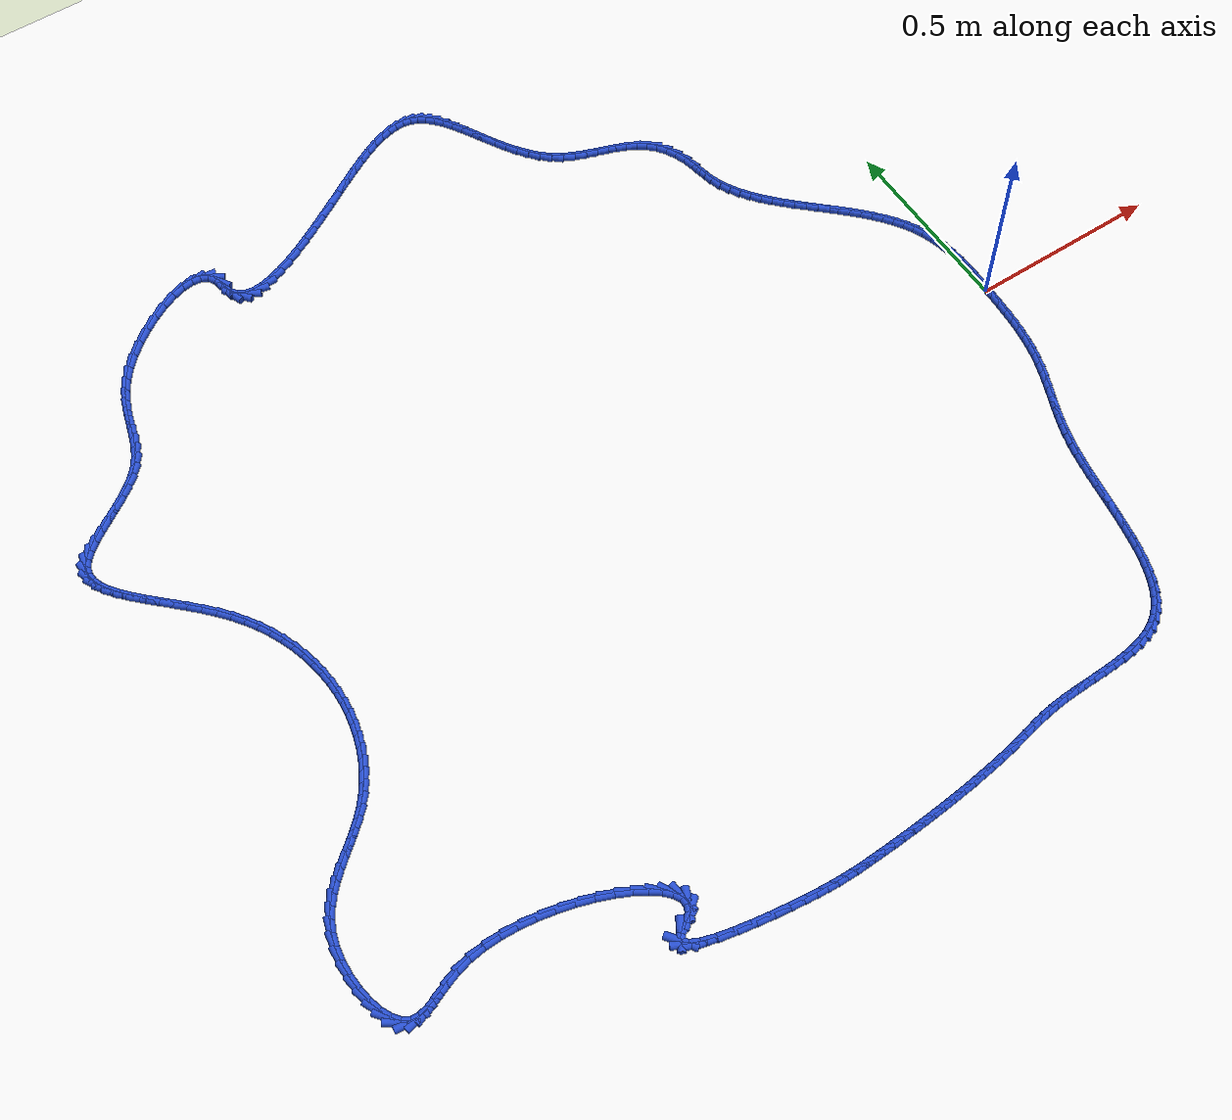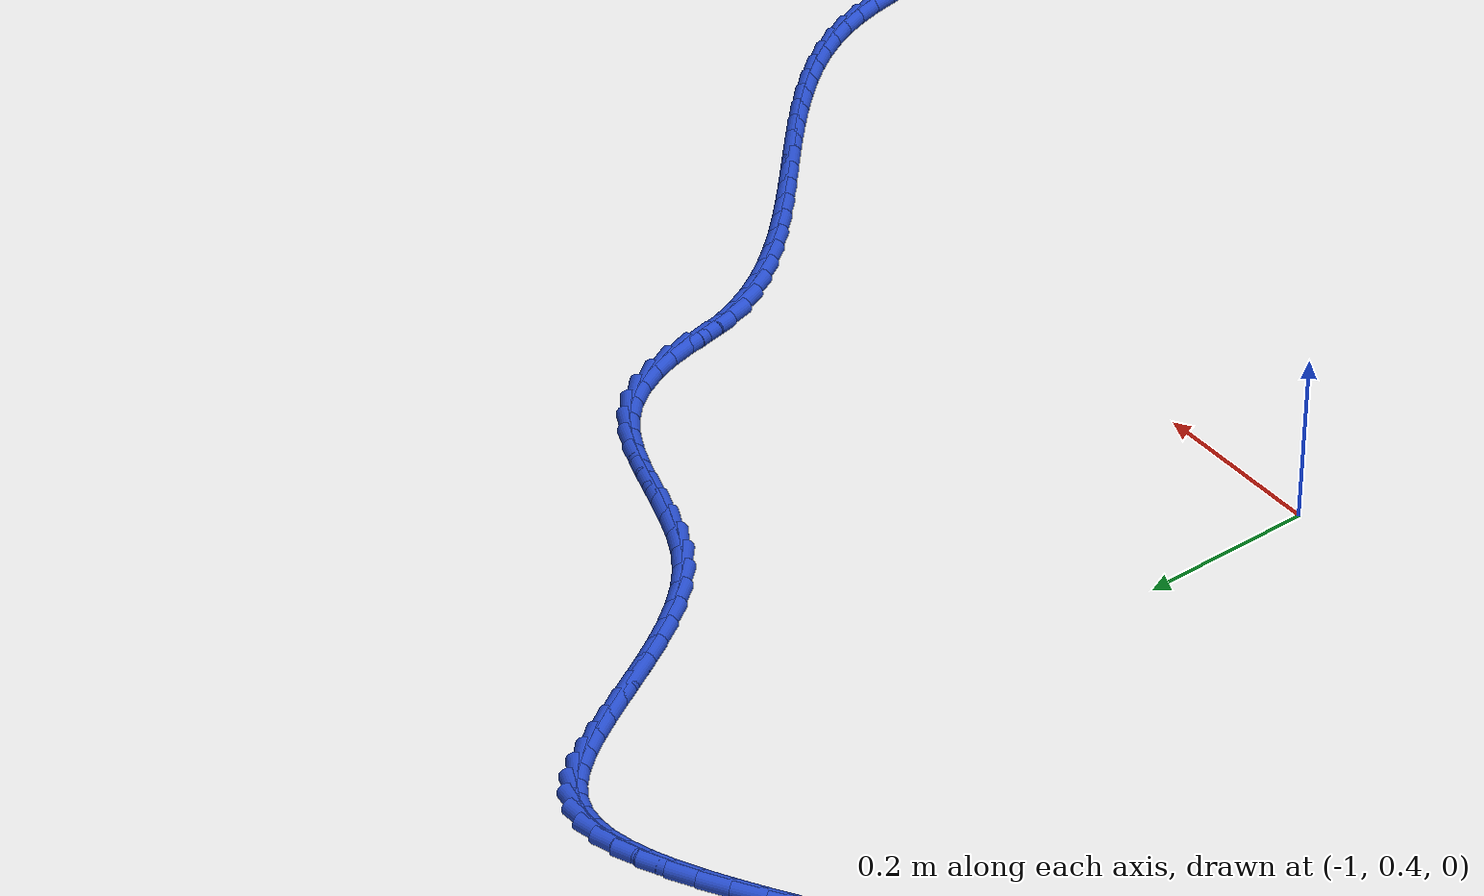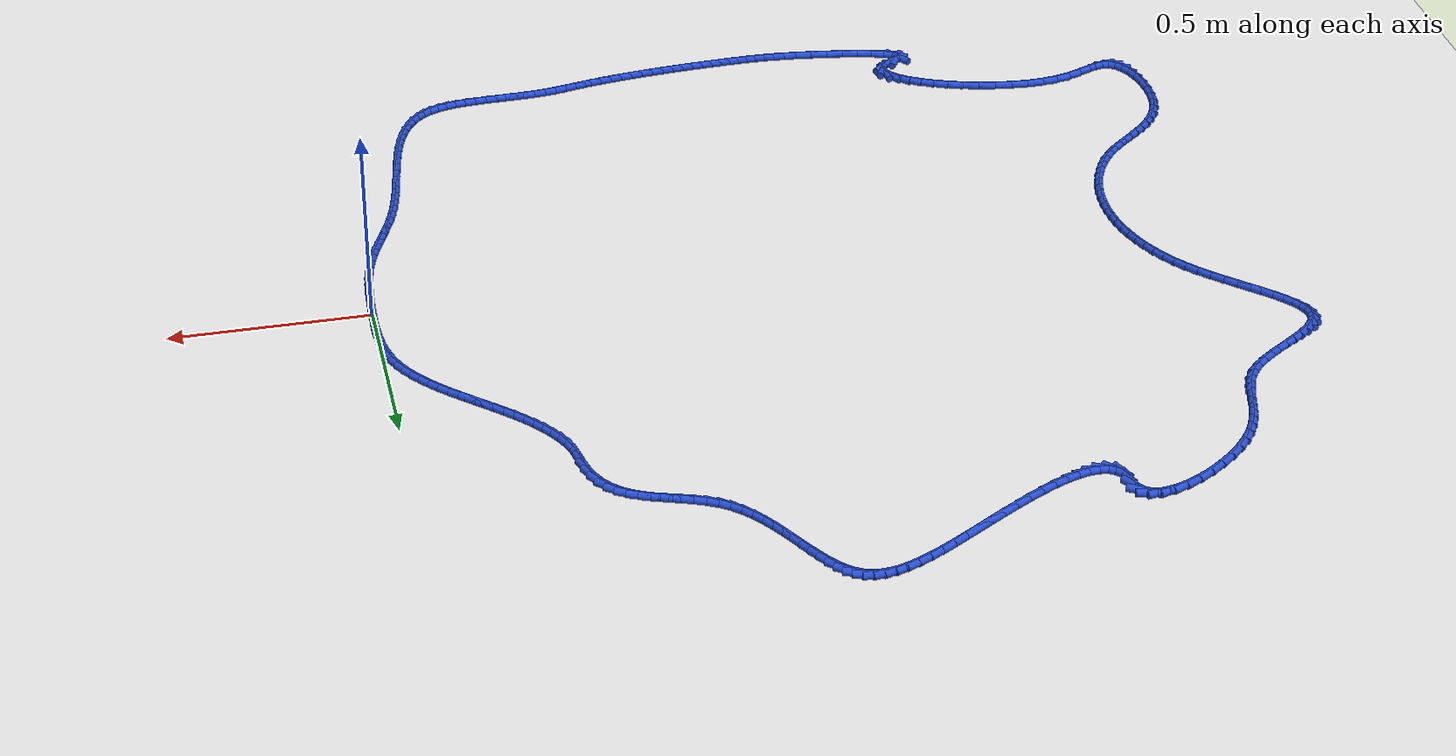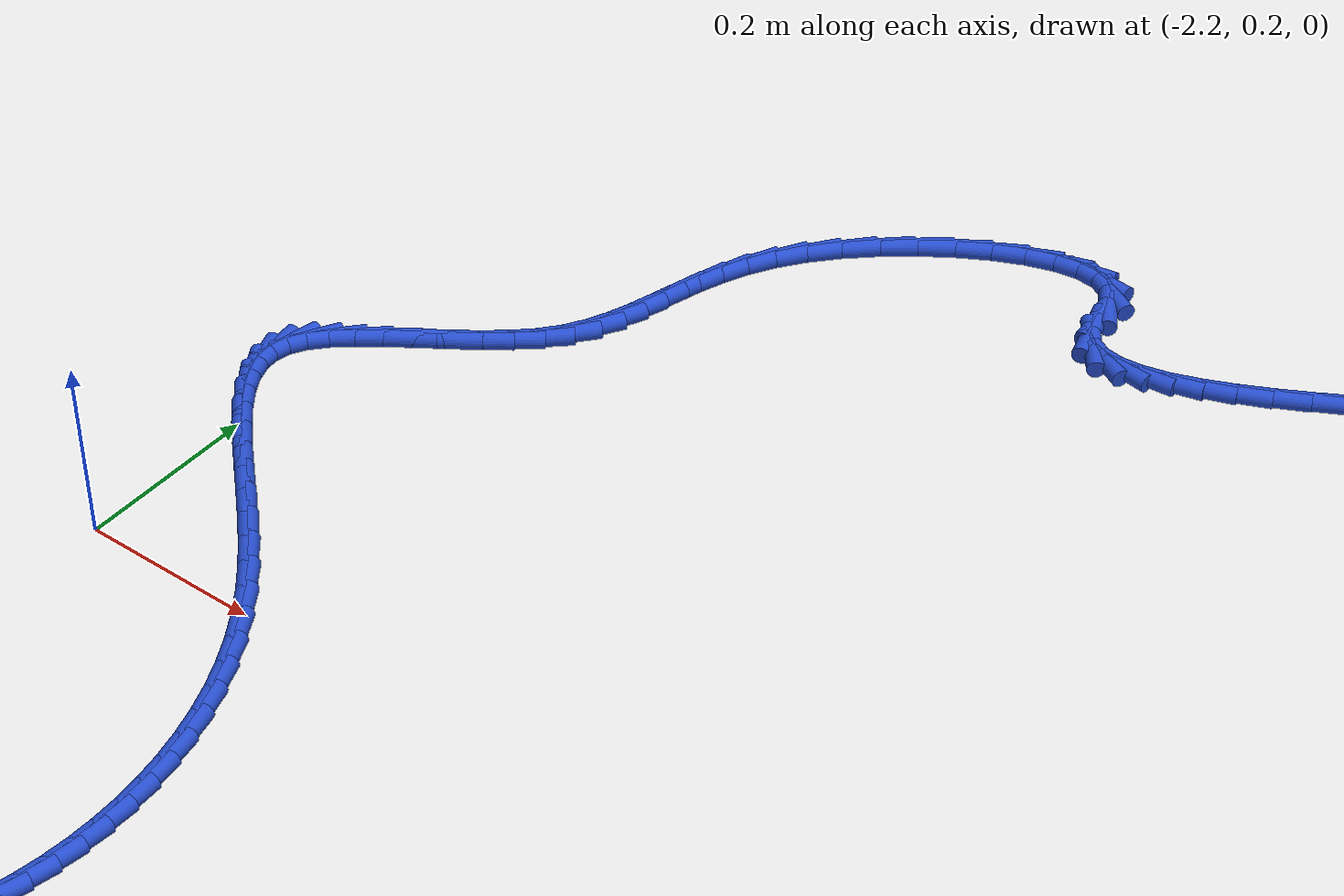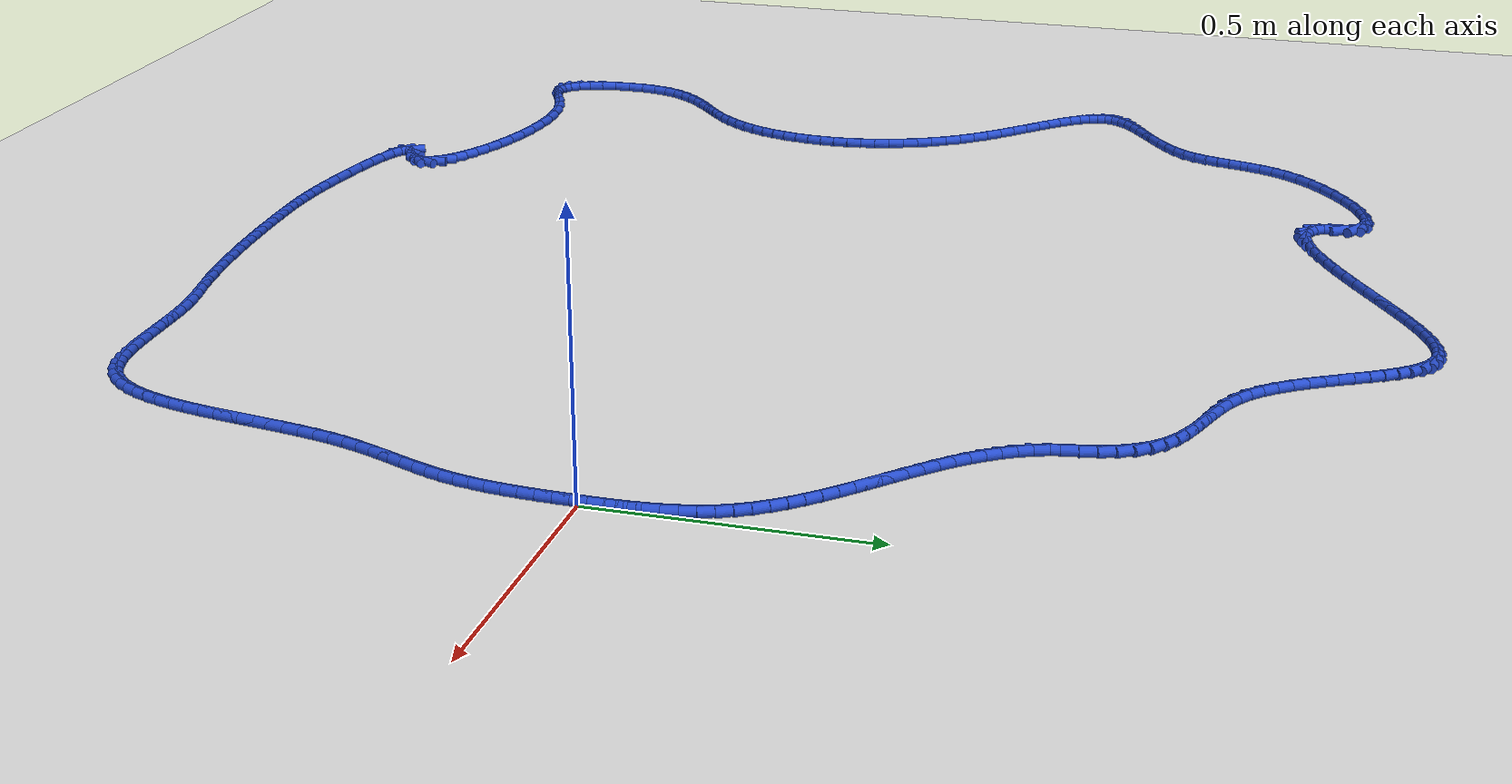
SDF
<sdf version="1.6">
 <world name="default">
  <light name="sun" type="directional">
   <pose>0 0 10 0 -0 0</pose>
   <diffuse>0.8 0.8 0.8 1</diffuse>
   <specular>0.2 0.2 0.2 1</specular>
   <attenuation>
    <range>1000</range>
    <constant>0.9</constant>
    <linear>0.01</linear>
    <quadratic>0.001</quadratic>
   </attenuation>
   <direction>-0.5 0.1 -0.9</direction>
  </light>
  <model name="ground_plane">
   <static>1</static>
   <link name="link">
    <collision name="collision">
     <geometry><plane><normal>0 0 1</normal><size>100 100</size></plane></geometry>
     <surface><friction><ode><mu>100</mu><mu2>50</mu2></ode></friction></surface>
    </collision>
    <visual name="visual">
     <cast_shadows>0</cast_shadows>
     <geometry><plane><normal>0 0 1</normal><size>100 100</size></plane></geometry>
     <material>
      <script><uri>file://media/materials/scripts/gazebo.material</uri><name>Gazebo/WhiteGlow</name></script>
     </material>
    </visual>
   </link>
  </model>
  <gravity>0 0 -9.8</gravity>
  <magnetic_field>6e-06 2.3e-05 -4.2e-05</magnetic_field>
  <atmosphere type="adiabatic"/>
  <physics name="default_physics" default="0" type="ode">
   <max_step_size>0.001</max_step_size>
   <real_time_factor>1</real_time_factor>
   <real_time_update_rate>1000</real_time_update_rate>
  </physics>
  <scene><ambient>0.4 0.4 0.4 1</ambient><background>0.7 0.7 0.7 1</background><shadows>1</shadows></scene>
  <spherical_coordinates>
   <surface_model>EARTH_WGS84</surface_model>
   <latitude_deg>0</latitude_deg>
   <longitude_deg>0</longitude_deg>
   <elevation>0</elevation>
   <heading_deg>0</heading_deg>
  </spherical_coordinates>
  <model name="line">
   <link name="link_0">
    <pose>-6.315477654728063e-18 -5.551115123125783e-17 0.01 0 1.57 1.5521799722568603</pose>
    <collision name="collision">
     <geometry><cylinder><radius>0.01</radius><length>0.08</length></cylinder></geometry>
    </collision>
    <visual name="visual">
     <material>
      <script><name>Gazebo/Blue</name><uri>file://media/materials/scripts/gazebo.material</uri></script>
     </material>
     <geometry><cylinder><radius>0.01</radius><length>0.08</length></cylinder></geometry>
    </visual>
   </link>
   <link name="link_1">
    <pose>0.0005496870128518633 0.02952369159235073 0.01 0 1.57 1.5698375794840973</pose>
    <collision name="collision">
     <geometry><cylinder><radius>0.01</radius><length>0.08</length></cylinder></geometry>
    </collision>
    <visual name="visual">
     <material>
      <script><name>Gazebo/Blue</name><uri>file://media/materials/scripts/gazebo.material</uri></script>
     </material>
     <geometry><cylinder><radius>0.01</radius><length>0.08</length></cylinder></geometry>
    </visual>
   </link>
   <link name="link_2">
    <pose>0.0005779772166571195 0.059031148686111944 0.01 0 1.57 -1.544561334173158</pose>
    <collision name="collision">
     <geometry><cylinder><radius>0.01</radius><length>0.08</length></cylinder></geometry>
    </collision>
    <visual name="visual">
     <material>
      <script><name>Gazebo/Blue</name><uri>file://media/materials/scripts/gazebo.material</uri></script>
     </material>
     <geometry><cylinder><radius>0.01</radius><length>0.08</length></cylinder></geometry>
    </visual>
   </link>
   <link name="link_3">
    <pose>-0.0001920356625880761 0.08837501861110357 0.01 0 1.57 -1.507325512380247</pose>
    <collision name="collision">
     <geometry><cylinder><radius>0.01</radius><length>0.08</length></cylinder></geometry>
    </collision>
    <visual name="visual">
     <material>
      <script><name>Gazebo/Blue</name><uri>file://media/materials/scripts/gazebo.material</uri></script>
     </material>
     <geometry><cylinder><radius>0.01</radius><length>0.08</length></cylinder></geometry>
    </visual>
   </link>
   <link name="link_4">
    <pose>-0.002037257898887562 0.1174079486971456 0.01 0 1.57 -1.4593655760137818</pose>
    <collision name="collision">
     <geometry><cylinder><radius>0.01</radius><length>0.08</length></cylinder></geometry>
    </collision>
    <visual name="visual">
     <material>
      <script><name>Gazebo/Blue</name><uri>file://media/materials/scripts/gazebo.material</uri></script>
     </material>
     <geometry><cylinder><radius>0.01</radius><length>0.08</length></cylinder></geometry>
    </visual>
   </link>
   <link name="link_5">
    <pose>-0.005234595766245171 0.145982586274058 0.01 0 1.57 -1.3999180756269227</pose>
    <collision name="collision">
     <geometry><cylinder><radius>0.01</radius><length>0.08</length></cylinder></geometry>
    </collision>
    <visual name="visual">
     <material>
      <script><name>Gazebo/Blue</name><uri>file://media/materials/scripts/gazebo.material</uri></script>
     </material>
     <geometry><cylinder><radius>0.01</radius><length>0.08</length></cylinder></geometry>
    </visual>
   </link>
   <link name="link_6">
    <pose>-0.010060955538664755 0.17395157867166086 0.01 0 1.57 -1.3282990773244032</pose>
    <collision name="collision">
     <geometry><cylinder><radius>0.01</radius><length>0.08</length></cylinder></geometry>
    </collision>
    <visual name="visual">
     <material>
      <script><name>Gazebo/Blue</name><uri>file://media/materials/scripts/gazebo.material</uri></script>
     </material>
     <geometry><cylinder><radius>0.01</radius><length>0.08</length></cylinder></geometry>
    </visual>
   </link>
   <link name="link_7">
    <pose>-0.016793243490150142 0.20116757321977416 0.01 0 1.57 -1.24415492661356</pose>
    <collision name="collision">
     <geometry><cylinder><radius>0.01</radius><length>0.08</length></cylinder></geometry>
    </collision>
    <visual name="visual">
     <material>
      <script><name>Gazebo/Blue</name><uri>file://media/materials/scripts/gazebo.material</uri></script>
     </material>
     <geometry><cylinder><radius>0.01</radius><length>0.08</length></cylinder></geometry>
    </visual>
   </link>
   <link name="link_8">
    <pose>-0.025708365894705165 0.22748321724821777 0.01 0 1.57 -1.1502471378170327</pose>
    <collision name="collision">
     <geometry><cylinder><radius>0.01</radius><length>0.08</length></cylinder></geometry>
    </collision>
    <visual name="visual">
     <material>
      <script><name>Gazebo/Blue</name><uri>file://media/materials/scripts/gazebo.material</uri></script>
     </material>
     <geometry><cylinder><radius>0.01</radius><length>0.08</length></cylinder></geometry>
    </visual>
   </link>
   <link name="link_9">
    <pose>-0.03702209515663555 0.25278047668638326 0.01 0 1.57 -1.061879694904122</pose>
    <collision name="collision">
     <geometry><cylinder><radius>0.01</radius><length>0.08</length></cylinder></geometry>
    </collision>
    <visual name="visual">
     <material>
      <script><name>Gazebo/Blue</name><uri>file://media/materials/scripts/gazebo.material</uri></script>
     </material>
     <geometry><cylinder><radius>0.01</radius><length>0.08</length></cylinder></geometry>
    </visual>
   </link>
   <link name="link_10">
    <pose>-0.050596871207091575 0.2771107687571461 0.01 0 1.57 -0.9851186091933795</pose>
    <collision name="collision">
     <geometry><cylinder><radius>0.01</radius><length>0.08</length></cylinder></geometry>
    </collision>
    <visual name="visual">
     <material>
      <script><name>Gazebo/Blue</name><uri>file://media/materials/scripts/gazebo.material</uri></script>
     </material>
     <geometry><cylinder><radius>0.01</radius><length>0.08</length></cylinder></geometry>
    </visual>
   </link>
   <link name="link_11">
    <pose>-0.06616848016789426 0.3005862513552592 0.01 0 1.57 -0.9201719248379593</pose>
    <collision name="collision">
     <geometry><cylinder><radius>0.01</radius><length>0.08</length></cylinder></geometry>
    </collision>
    <visual name="visual">
     <material>
      <script><name>Gazebo/Blue</name><uri>file://media/materials/scripts/gazebo.material</uri></script>
     </material>
     <geometry><cylinder><radius>0.01</radius><length>0.08</length></cylinder></geometry>
    </visual>
   </link>
   <link name="link_12">
    <pose>-0.08347254576923875 0.3233191602552997 0.01 0 1.57 -0.8666974226638244</pose>
    <collision name="collision">
     <geometry><cylinder><radius>0.01</radius><length>0.08</length></cylinder></geometry>
    </collision>
    <visual name="visual">
     <material>
      <script><name>Gazebo/Blue</name><uri>file://media/materials/scripts/gazebo.material</uri></script>
     </material>
     <geometry><cylinder><radius>0.01</radius><length>0.08</length></cylinder></geometry>
    </visual>
   </link>
   <link name="link_13">
    <pose>-0.10224469174132038 0.3454217312318451 0.01 0 1.57 -0.824084492415108</pose>
    <collision name="collision">
     <geometry><cylinder><radius>0.01</radius><length>0.08</length></cylinder></geometry>
    </collision>
    <visual name="visual">
     <material>
      <script><name>Gazebo/Blue</name><uri>file://media/materials/scripts/gazebo.material</uri></script>
     </material>
     <geometry><cylinder><radius>0.01</radius><length>0.08</length></cylinder></geometry>
    </visual>
   </link>
   <link name="link_14">
    <pose>-0.12222054181433459 0.367006200059473 0.01 0 1.57 -0.7916561214176688</pose>
    <collision name="collision">
     <geometry><cylinder><radius>0.01</radius><length>0.08</length></cylinder></geometry>
    </collision>
    <visual name="visual">
     <material>
      <script><name>Gazebo/Blue</name><uri>file://media/materials/scripts/gazebo.material</uri></script>
     </material>
     <geometry><cylinder><radius>0.01</radius><length>0.08</length></cylinder></geometry>
    </visual>
   </link>
   <link name="link_15">
    <pose>-0.14313571971847638 0.3881848025127604 0.01 0 1.57 -0.7687980184502529</pose>
    <collision name="collision">
     <geometry><cylinder><radius>0.01</radius><length>0.08</length></cylinder></geometry>
    </collision>
    <visual name="visual">
     <material>
      <script><name>Gazebo/Blue</name><uri>file://media/materials/scripts/gazebo.material</uri></script>
     </material>
     <geometry><cylinder><radius>0.01</radius><length>0.08</length></cylinder></geometry>
    </visual>
   </link>
   <link name="link_16">
    <pose>-0.16472584918394126 0.40906977436628494 0.01 0 1.57 -0.755032846931287</pose>
    <collision name="collision">
     <geometry><cylinder><radius>0.01</radius><length>0.08</length></cylinder></geometry>
    </collision>
    <visual name="visual">
     <material>
      <script><name>Gazebo/Blue</name><uri>file://media/materials/scripts/gazebo.material</uri></script>
     </material>
     <geometry><cylinder><radius>0.01</radius><length>0.08</length></cylinder></geometry>
    </visual>
   </link>
   <link name="link_17">
    <pose>-0.1867265539409245 0.4297733513946239 0.01 0 1.57 -0.7500589999360706</pose>
    <collision name="collision">
     <geometry><cylinder><radius>0.01</radius><length>0.08</length></cylinder></geometry>
    </collision>
    <visual name="visual">
     <material>
      <script><name>Gazebo/Blue</name><uri>file://media/materials/scripts/gazebo.material</uri></script>
     </material>
     <geometry><cylinder><radius>0.01</radius><length>0.08</length></cylinder></geometry>
    </visual>
   </link>
   <link name="link_18">
    <pose>-0.20887345771962124 0.45040776937235455 0.01 0 1.57 -0.7537685517264915</pose>
    <collision name="collision">
     <geometry><cylinder><radius>0.01</radius><length>0.08</length></cylinder></geometry>
    </collision>
    <visual name="visual">
     <material>
      <script><name>Gazebo/Blue</name><uri>file://media/materials/scripts/gazebo.material</uri></script>
     </material>
     <geometry><cylinder><radius>0.01</radius><length>0.08</length></cylinder></geometry>
    </visual>
   </link>
   <link name="link_19">
    <pose>-0.23090218425022702 0.47108526407405465 0.01 0 1.57 -0.7662530137304234</pose>
    <collision name="collision">
     <geometry><cylinder><radius>0.01</radius><length>0.08</length></cylinder></geometry>
    </collision>
    <visual name="visual">
     <material>
      <script><name>Gazebo/Blue</name><uri>file://media/materials/scripts/gazebo.material</uri></script>
     </material>
     <geometry><cylinder><radius>0.01</radius><length>0.08</length></cylinder></geometry>
    </visual>
   </link>
   <link name="link_20">
    <pose>-0.25254835726293684 0.49191807127430104 0.01 0 1.57 -0.7877998977861596</pose>
    <collision name="collision">
     <geometry><cylinder><radius>0.01</radius><length>0.08</length></cylinder></geometry>
    </collision>
    <visual name="visual">
     <material>
      <script><name>Gazebo/Blue</name><uri>file://media/materials/scripts/gazebo.material</uri></script>
     </material>
     <geometry><cylinder><radius>0.01</radius><length>0.08</length></cylinder></geometry>
    </visual>
   </link>
   <link name="link_21">
    <pose>-0.2735476004879463 0.5130184267476716 0.01 0 1.57 -0.8188777530315653</pose>
    <collision name="collision">
     <geometry><cylinder><radius>0.01</radius><length>0.08</length></cylinder></geometry>
    </collision>
    <visual name="visual">
     <material>
      <script><name>Gazebo/Blue</name><uri>file://media/materials/scripts/gazebo.material</uri></script>
     </material>
     <geometry><cylinder><radius>0.01</radius><length>0.08</length></cylinder></geometry>
    </visual>
   </link>
   <link name="link_22">
    <pose>-0.2936355376554504 0.5344985662687433 0.01 0 1.57 -0.8601016999954341</pose>
    <collision name="collision">
     <geometry><cylinder><radius>0.01</radius><length>0.08</length></cylinder></geometry>
    </collision>
    <visual name="visual">
     <material>
      <script><name>Gazebo/Blue</name><uri>file://media/materials/scripts/gazebo.material</uri></script>
     </material>
     <geometry><cylinder><radius>0.01</radius><length>0.08</length></cylinder></geometry>
    </visual>
   </link>
   <link name="link_23">
    <pose>-0.3125477924956447 0.5564707256120938 0.01 0 1.57 -0.9121653038584405</pose>
    <collision name="collision">
     <geometry><cylinder><radius>0.01</radius><length>0.08</length></cylinder></geometry>
    </collision>
    <visual name="visual">
     <material>
      <script><name>Gazebo/Blue</name><uri>file://media/materials/scripts/gazebo.material</uri></script>
     </material>
     <geometry><cylinder><radius>0.01</radius><length>0.08</length></cylinder></geometry>
    </visual>
   </link>
   <link name="link_24">
    <pose>-0.3300199887387243 0.5790471405523003 0.01 0 1.57 -0.9757191790452033</pose>
    <collision name="collision">
     <geometry><cylinder><radius>0.01</radius><length>0.08</length></cylinder></geometry>
    </collision>
    <visual name="visual">
     <material>
      <script><name>Gazebo/Blue</name><uri>file://media/materials/scripts/gazebo.material</uri></script>
     </material>
     <geometry><cylinder><radius>0.01</radius><length>0.08</length></cylinder></geometry>
    </visual>
   </link>
   <link name="link_25">
    <pose>-0.3457877501148845 0.6023400468639404 0.01 0 1.57 -1.051176572079485</pose>
    <collision name="collision">
     <geometry><cylinder><radius>0.01</radius><length>0.08</length></cylinder></geometry>
    </collision>
    <visual name="visual">
     <material>
      <script><name>Gazebo/Blue</name><uri>file://media/materials/scripts/gazebo.material</uri></script>
     </material>
     <geometry><cylinder><radius>0.01</radius><length>0.08</length></cylinder></geometry>
    </visual>
   </link>
   <link name="link_26">
    <pose>-0.3595867003543206 0.626461680321591 0.01 0 1.57 -1.138440831098176</pose>
    <collision name="collision">
     <geometry><cylinder><radius>0.01</radius><length>0.08</length></cylinder></geometry>
    </collision>
    <visual name="visual">
     <material>
      <script><name>Gazebo/Blue</name><uri>file://media/materials/scripts/gazebo.material</uri></script>
     </material>
     <geometry><cylinder><radius>0.01</radius><length>0.08</length></cylinder></geometry>
    </visual>
   </link>
   <link name="link_27">
    <pose>-0.37115246318722794 0.6515242766998299 0.01 0 1.57 -1.2365909440726583</pose>
    <collision name="collision">
     <geometry><cylinder><radius>0.01</radius><length>0.08</length></cylinder></geometry>
    </collision>
    <visual name="visual">
     <material>
      <script><name>Gazebo/Blue</name><uri>file://media/materials/scripts/gazebo.material</uri></script>
     </material>
     <geometry><cylinder><radius>0.01</radius><length>0.08</length></cylinder></geometry>
    </visual>
   </link>
   <link name="link_28">
    <pose>-0.3802206623438018 0.6776400717732346 0.01 0 1.57 -1.3410440412815732</pose>
    <collision name="collision">
     <geometry><cylinder><radius>0.01</radius><length>0.08</length></cylinder></geometry>
    </collision>
    <visual name="visual">
     <material>
      <script><name>Gazebo/Blue</name><uri>file://media/materials/scripts/gazebo.material</uri></script>
     </material>
     <geometry><cylinder><radius>0.01</radius><length>0.08</length></cylinder></geometry>
    </visual>
   </link>
   <link name="link_29">
    <pose>-0.3865970740748618 0.7049034331302354 0.01 0 1.57 -1.394222935068772</pose>
    <collision name="collision">
     <geometry><cylinder><radius>0.01</radius><length>0.08</length></cylinder></geometry>
    </collision>
    <visual name="visual">
     <material>
      <script><name>Gazebo/Blue</name><uri>file://media/materials/scripts/gazebo.material</uri></script>
     </material>
     <geometry><cylinder><radius>0.01</radius><length>0.08</length></cylinder></geometry>
    </visual>
   </link>
   <link name="link_30">
    <pose>-0.39161394668679966 0.7330199285471655 0.01 0 1.57 -1.346421298038048</pose>
    <collision name="collision">
     <geometry><cylinder><radius>0.01</radius><length>0.08</length></cylinder></geometry>
    </collision>
    <visual name="visual">
     <material>
      <script><name>Gazebo/Blue</name><uri>file://media/materials/scripts/gazebo.material</uri></script>
     </material>
     <geometry><cylinder><radius>0.01</radius><length>0.08</length></cylinder></geometry>
    </visual>
   </link>
   <link name="link_31">
    <pose>-0.3980717817207699 0.761316741160868 0.01 0 1.57 -1.231528642623839</pose>
    <collision name="collision">
     <geometry><cylinder><radius>0.01</radius><length>0.08</length></cylinder></geometry>
    </collision>
    <visual name="visual">
     <material>
      <script><name>Gazebo/Blue</name><uri>file://media/materials/scripts/gazebo.material</uri></script>
     </material>
     <geometry><cylinder><radius>0.01</radius><length>0.08</length></cylinder></geometry>
    </visual>
   </link>
   <link name="link_32">
    <pose>-0.40783179814437837 0.7889723178215621 0.01 0 1.57 -1.1016841542292362</pose>
    <collision name="collision">
     <geometry><cylinder><radius>0.01</radius><length>0.08</length></cylinder></geometry>
    </collision>
    <visual name="visual">
     <material>
      <script><name>Gazebo/Blue</name><uri>file://media/materials/scripts/gazebo.material</uri></script>
     </material>
     <geometry><cylinder><radius>0.01</radius><length>0.08</length></cylinder></geometry>
    </visual>
   </link>
   <link name="link_33">
    <pose>-0.42098826657242644 0.8149296656260628 0.01 0 1.57 -0.9530964984346205</pose>
    <collision name="collision">
     <geometry><cylinder><radius>0.01</radius><length>0.08</length></cylinder></geometry>
    </collision>
    <visual name="visual">
     <material>
      <script><name>Gazebo/Blue</name><uri>file://media/materials/scripts/gazebo.material</uri></script>
     </material>
     <geometry><cylinder><radius>0.01</radius><length>0.08</length></cylinder></geometry>
    </visual>
   </link>
   <link name="link_34">
    <pose>-0.4374549483786912 0.8381077394394795 0.01 0 1.57 -0.7789869360752086</pose>
    <collision name="collision">
     <geometry><cylinder><radius>0.01</radius><length>0.08</length></cylinder></geometry>
    </collision>
    <visual name="visual">
     <material>
      <script><name>Gazebo/Blue</name><uri>file://media/materials/scripts/gazebo.material</uri></script>
     </material>
     <geometry><cylinder><radius>0.01</radius><length>0.08</length></cylinder></geometry>
    </visual>
   </link>
   <link name="link_35">
    <pose>-0.4571206233203562 0.8575228551155695 0.01 0 1.57 -0.6121597621778474</pose>
    <collision name="collision">
     <geometry><cylinder><radius>0.01</radius><length>0.08</length></cylinder></geometry>
    </collision>
    <visual name="visual">
     <material>
      <script><name>Gazebo/Blue</name><uri>file://media/materials/scripts/gazebo.material</uri></script>
     </material>
     <geometry><cylinder><radius>0.01</radius><length>0.08</length></cylinder></geometry>
    </visual>
   </link>
   <link name="link_36">
    <pose>-0.4795897762439565 0.8732993125916804 0.01 0 1.57 -0.4834493400329303</pose>
    <collision name="collision">
     <geometry><cylinder><radius>0.01</radius><length>0.08</length></cylinder></geometry>
    </collision>
    <visual name="visual">
     <material>
      <script><name>Gazebo/Blue</name><uri>file://media/materials/scripts/gazebo.material</uri></script>
     </material>
     <geometry><cylinder><radius>0.01</radius><length>0.08</length></cylinder></geometry>
    </visual>
   </link>
   <link name="link_37">
    <pose>-0.5042863390584588 0.8862650817393635 0.01 0 1.57 -0.3953471236145597</pose>
    <collision name="collision">
     <geometry><cylinder><radius>0.01</radius><length>0.08</length></cylinder></geometry>
    </collision>
    <visual name="visual">
     <material>
      <script><name>Gazebo/Blue</name><uri>file://media/materials/scripts/gazebo.material</uri></script>
     </material>
     <geometry><cylinder><radius>0.01</radius><length>0.08</length></cylinder></geometry>
    </visual>
   </link>
   <link name="link_38">
    <pose>-0.5306313605147939 0.8972593689774838 0.01 0 1.57 -0.3453224569784814</pose>
    <collision name="collision">
     <geometry><cylinder><radius>0.01</radius><length>0.08</length></cylinder></geometry>
    </collision>
    <visual name="visual">
     <material>
      <script><name>Gazebo/Blue</name><uri>file://media/materials/scripts/gazebo.material</uri></script>
     </material>
     <geometry><cylinder><radius>0.01</radius><length>0.08</length></cylinder></geometry>
    </visual>
   </link>
   <link name="link_39">
    <pose>-0.5580458893638928 0.9071213807249056 0.01 0 1.57 -0.3303449713938625</pose>
    <collision name="collision">
     <geometry><cylinder><radius>0.01</radius><length>0.08</length></cylinder></geometry>
    </collision>
    <visual name="visual">
     <material>
      <script><name>Gazebo/Blue</name><uri>file://media/materials/scripts/gazebo.material</uri></script>
     </material>
     <geometry><cylinder><radius>0.01</radius><length>0.08</length></cylinder></geometry>
    </visual>
   </link>
   <link name="link_40">
    <pose>-0.5859509743566863 0.9166903234004934 0.01 0 1.57 -0.3487684655081734</pose>
    <collision name="collision">
     <geometry><cylinder><radius>0.01</radius><length>0.08</length></cylinder></geometry>
    </collision>
    <visual name="visual">
     <material>
      <script><name>Gazebo/Blue</name><uri>file://media/materials/scripts/gazebo.material</uri></script>
     </material>
     <geometry><cylinder><radius>0.01</radius><length>0.08</length></cylinder></geometry>
    </visual>
   </link>
   <link name="link_41">
    <pose>-0.6137676642441052 0.9268054034231114 0.01 0 1.57 -0.40068304663403403</pose>
    <collision name="collision">
     <geometry><cylinder><radius>0.01</radius><length>0.08</length></cylinder></geometry>
    </collision>
    <visual name="visual">
     <material>
      <script><name>Gazebo/Blue</name><uri>file://media/materials/scripts/gazebo.material</uri></script>
     </material>
     <geometry><cylinder><radius>0.01</radius><length>0.08</length></cylinder></geometry>
    </visual>
   </link>
   <link name="link_42">
    <pose>-0.6409170077770807 0.9383058272116248 0.01 0 1.57 -0.4872488547449545</pose>
    <collision name="collision">
     <geometry><cylinder><radius>0.01</radius><length>0.08</length></cylinder></geometry>
    </collision>
    <visual name="visual">
     <material>
      <script><name>Gazebo/Blue</name><uri>file://media/materials/scripts/gazebo.material</uri></script>
     </material>
     <geometry><cylinder><radius>0.01</radius><length>0.08</length></cylinder></geometry>
    </visual>
   </link>
   <link name="link_43">
    <pose>-0.6668200537065435 0.9520308011848979 0.01 0 1.57 -0.6084066487717664</pose>
    <collision name="collision">
     <geometry><cylinder><radius>0.01</radius><length>0.08</length></cylinder></geometry>
    </collision>
    <visual name="visual">
     <material>
      <script><name>Gazebo/Blue</name><uri>file://media/materials/scripts/gazebo.material</uri></script>
     </material>
     <geometry><cylinder><radius>0.01</radius><length>0.08</length></cylinder></geometry>
    </visual>
   </link>
   <link name="link_44">
    <pose>-0.6909050541292129 0.96880720377337 0.01 0 1.57 -0.7390649176321223</pose>
    <collision name="collision">
     <geometry><cylinder><radius>0.01</radius><length>0.08</length></cylinder></geometry>
    </collision>
    <visual name="visual">
     <material>
      <script><name>Gazebo/Blue</name><uri>file://media/materials/scripts/gazebo.material</uri></script>
     </material>
     <geometry><cylinder><radius>0.01</radius><length>0.08</length></cylinder></geometry>
    </visual>
   </link>
   <link name="link_45">
    <pose>-0.7129366236131514 0.988886254154824 0.01 0 1.57 -0.8459336072416772</pose>
    <collision name="collision">
     <geometry><cylinder><radius>0.01</radius><length>0.08</length></cylinder></geometry>
    </collision>
    <visual name="visual">
     <material>
      <script><name>Gazebo/Blue</name><uri>file://media/materials/scripts/gazebo.material</uri></script>
     </material>
     <geometry><cylinder><radius>0.01</radius><length>0.08</length></cylinder></geometry>
    </visual>
   </link>
   <link name="link_46">
    <pose>-0.7331520311246378 1.0117102587988083 0.01 0 1.57 -0.9283470060510146</pose>
    <collision name="collision">
     <geometry><cylinder><radius>0.01</radius><length>0.08</length></cylinder></geometry>
    </collision>
    <visual name="visual">
     <material>
      <script><name>Gazebo/Blue</name><uri>file://media/materials/scripts/gazebo.material</uri></script>
     </material>
     <geometry><cylinder><radius>0.01</radius><length>0.08</length></cylinder></geometry>
    </visual>
   </link>
   <link name="link_47">
    <pose>-0.7518240000289094 1.0366608466185265 0.01 0 1.57 -0.9890455743865944</pose>
    <collision name="collision">
     <geometry><cylinder><radius>0.01</radius><length>0.08</length></cylinder></geometry>
    </collision>
    <visual name="visual">
     <material>
      <script><name>Gazebo/Blue</name><uri>file://media/materials/scripts/gazebo.material</uri></script>
     </material>
     <geometry><cylinder><radius>0.01</radius><length>0.08</length></cylinder></geometry>
    </visual>
   </link>
   <link name="link_48">
    <pose>-0.7692252536912018 1.0631196465271808 0.01 0 1.57 -1.0305360807766697</pose>
    <collision name="collision">
     <geometry><cylinder><radius>0.01</radius><length>0.08</length></cylinder></geometry>
    </collision>
    <visual name="visual">
     <material>
      <script><name>Gazebo/Blue</name><uri>file://media/materials/scripts/gazebo.material</uri></script>
     </material>
     <geometry><cylinder><radius>0.01</radius><length>0.08</length></cylinder></geometry>
    </visual>
   </link>
   <link name="link_49">
    <pose>-0.7856285154767519 1.0904682874379752 0.01 0 1.57 -1.0545187166941372</pose>
    <collision name="collision">
     <geometry><cylinder><radius>0.01</radius><length>0.08</length></cylinder></geometry>
    </collision>
    <visual name="visual">
     <material>
      <script><name>Gazebo/Blue</name><uri>file://media/materials/scripts/gazebo.material</uri></script>
     </material>
     <geometry><cylinder><radius>0.01</radius><length>0.08</length></cylinder></geometry>
    </visual>
   </link>
   <link name="link_50">
    <pose>-0.8013065087507969 1.1180883982641125 0.01 0 1.57 -1.0616362162556325</pose>
    <collision name="collision">
     <geometry><cylinder><radius>0.01</radius><length>0.08</length></cylinder></geometry>
    </collision>
    <visual name="visual">
     <material>
      <script><name>Gazebo/Blue</name><uri>file://media/materials/scripts/gazebo.material</uri></script>
     </material>
     <geometry><cylinder><radius>0.01</radius><length>0.08</length></cylinder></geometry>
    </visual>
   </link>
   <link name="link_51">
    <pose>-0.8165319568785724 1.145361607918796 0.01 0 1.57 -1.0512915503115228</pose>
    <collision name="collision">
     <geometry><cylinder><radius>0.01</radius><length>0.08</length></cylinder></geometry>
    </collision>
    <visual name="visual">
     <material>
      <script><name>Gazebo/Blue</name><uri>file://media/materials/scripts/gazebo.material</uri></script>
     </material>
     <geometry><cylinder><radius>0.01</radius><length>0.08</length></cylinder></geometry>
    </visual>
   </link>
   <link name="link_52">
    <pose>-0.8315775832253158 1.1716695453152286 0.01 0 1.57 -1.0213863920741342</pose>
    <collision name="collision">
     <geometry><cylinder><radius>0.01</radius><length>0.08</length></cylinder></geometry>
    </collision>
    <visual name="visual">
     <material>
      <script><name>Gazebo/Blue</name><uri>file://media/materials/scripts/gazebo.material</uri></script>
     </material>
     <geometry><cylinder><radius>0.01</radius><length>0.08</length></cylinder></geometry>
    </visual>
   </link>
   <link name="link_53">
    <pose>-0.8467161111562632 1.1963938393666138 0.01 0 1.57 -0.967903652109983</pose>
    <collision name="collision">
     <geometry><cylinder><radius>0.01</radius><length>0.08</length></cylinder></geometry>
    </collision>
    <visual name="visual">
     <material>
      <script><name>Gazebo/Blue</name><uri>file://media/materials/scripts/gazebo.material</uri></script>
     </material>
     <geometry><cylinder><radius>0.01</radius><length>0.08</length></cylinder></geometry>
    </visual>
   </link>
   <link name="link_54">
    <pose>-0.8622202640366514 1.2189161189861544 0.01 0 1.57 -0.8843749267099008</pose>
    <collision name="collision">
     <geometry><cylinder><radius>0.01</radius><length>0.08</length></cylinder></geometry>
    </collision>
    <visual name="visual">
     <material>
      <script><name>Gazebo/Blue</name><uri>file://media/materials/scripts/gazebo.material</uri></script>
     </material>
     <geometry><cylinder><radius>0.01</radius><length>0.08</length></cylinder></geometry>
    </visual>
   </link>
   <link name="link_55">
    <pose>-0.8783627652317172 1.2386180130870539 0.01 0 1.57 -0.7616777205165279</pose>
    <collision name="collision">
     <geometry><cylinder><radius>0.01</radius><length>0.08</length></cylinder></geometry>
    </collision>
    <visual name="visual">
     <material>
      <script><name>Gazebo/Blue</name><uri>file://media/materials/scripts/gazebo.material</uri></script>
     </material>
     <geometry><cylinder><radius>0.01</radius><length>0.08</length></cylinder></geometry>
    </visual>
   </link>
   <link name="link_56">
    <pose>-0.8954163381066966 1.254881150582515 0.01 0 1.57 -0.5898135988125783</pose>
    <collision name="collision">
     <geometry><cylinder><radius>0.01</radius><length>0.08</length></cylinder></geometry>
    </collision>
    <visual name="visual">
     <material>
      <script><name>Gazebo/Blue</name><uri>file://media/materials/scripts/gazebo.material</uri></script>
     </material>
     <geometry><cylinder><radius>0.01</radius><length>0.08</length></cylinder></geometry>
    </visual>
   </link>
   <link name="link_57">
    <pose>-0.9136537060268264 1.2670871603857412 0.01 0 1.57 -0.3718109992747777</pose>
    <collision name="collision">
     <geometry><cylinder><radius>0.01</radius><length>0.08</length></cylinder></geometry>
    </collision>
    <visual name="visual">
     <material>
      <script><name>Gazebo/Blue</name><uri>file://media/materials/scripts/gazebo.material</uri></script>
     </material>
     <geometry><cylinder><radius>0.01</radius><length>0.08</length></cylinder></geometry>
    </visual>
   </link>
   <link name="link_58">
    <pose>-0.9333081632375927 1.2747513780517328 0.01 0 1.57 -0.15383803340425217</pose>
    <collision name="collision">
     <geometry><cylinder><radius>0.01</radius><length>0.08</length></cylinder></geometry>
    </collision>
    <visual name="visual">
     <material>
      <script><name>Gazebo/Blue</name><uri>file://media/materials/scripts/gazebo.material</uri></script>
     </material>
     <geometry><cylinder><radius>0.01</radius><length>0.08</length></cylinder></geometry>
    </visual>
   </link>
   <link name="link_59">
    <pose>-0.9544252396581058 1.2780258598558059 0.01 0 1.57 0.034275042335543</pose>
    <collision name="collision">
     <geometry><cylinder><radius>0.01</radius><length>0.08</length></cylinder></geometry>
    </collision>
    <visual name="visual">
     <material>
      <script><name>Gazebo/Blue</name><uri>file://media/materials/scripts/gazebo.material</uri></script>
     </material>
     <geometry><cylinder><radius>0.01</radius><length>0.08</length></cylinder></geometry>
    </visual>
   </link>
   <link name="link_60">
    <pose>-0.9769946338181594 1.2772519898497907 0.01 0 1.57 0.18448960536201323</pose>
    <collision name="collision">
     <geometry><cylinder><radius>0.01</radius><length>0.08</length></cylinder></geometry>
    </collision>
    <visual name="visual">
     <material>
      <script><name>Gazebo/Blue</name><uri>file://media/materials/scripts/gazebo.material</uri></script>
     </material>
     <geometry><cylinder><radius>0.01</radius><length>0.08</length></cylinder></geometry>
    </visual>
   </link>
   <link name="link_61">
    <pose>-1.0010060350357195 1.2727711833234134 0.01 0 1.57 0.29913367753106435</pose>
    <collision name="collision">
     <geometry><cylinder><radius>0.01</radius><length>0.08</length></cylinder></geometry>
    </collision>
    <visual name="visual">
     <material>
      <script><name>Gazebo/Blue</name><uri>file://media/materials/scripts/gazebo.material</uri></script>
     </material>
     <geometry><cylinder><radius>0.01</radius><length>0.08</length></cylinder></geometry>
    </visual>
   </link>
   <link name="link_62">
    <pose>-1.0264491326287508 1.2649248555663986 0.01 0 1.57 0.38449962003850335</pose>
    <collision name="collision">
     <geometry><cylinder><radius>0.01</radius><length>0.08</length></cylinder></geometry>
    </collision>
    <visual name="visual">
     <material>
      <script><name>Gazebo/Blue</name><uri>file://media/materials/scripts/gazebo.material</uri></script>
     </material>
     <geometry><cylinder><radius>0.01</radius><length>0.08</length></cylinder></geometry>
    </visual>
   </link>
   <link name="link_63">
    <pose>-1.0533136159152192 1.2540544218684704 0.01 0 1.57 0.4469695712005826</pose>
    <collision name="collision">
     <geometry><cylinder><radius>0.01</radius><length>0.08</length></cylinder></geometry>
    </collision>
    <visual name="visual">
     <material>
      <script><name>Gazebo/Blue</name><uri>file://media/materials/scripts/gazebo.material</uri></script>
     </material>
     <geometry><cylinder><radius>0.01</radius><length>0.08</length></cylinder></geometry>
    </visual>
   </link>
   <link name="link_64">
    <pose>-1.0815891742130905 1.2405012975193548 0.01 0 1.57 0.49171412083916854</pose>
    <collision name="collision">
     <geometry><cylinder><radius>0.01</radius><length>0.08</length></cylinder></geometry>
    </collision>
    <visual name="visual">
     <material>
      <script><name>Gazebo/Blue</name><uri>file://media/materials/scripts/gazebo.material</uri></script>
     </material>
     <geometry><cylinder><radius>0.01</radius><length>0.08</length></cylinder></geometry>
    </visual>
   </link>
   <link name="link_65">
    <pose>-1.1112654968403295 1.2246068978087767 0.01 0 1.57 0.5225805666138809</pose>
    <collision name="collision">
     <geometry><cylinder><radius>0.01</radius><length>0.08</length></cylinder></geometry>
    </collision>
    <visual name="visual">
     <material>
      <script><name>Gazebo/Blue</name><uri>file://media/materials/scripts/gazebo.material</uri></script>
     </material>
     <geometry><cylinder><radius>0.01</radius><length>0.08</length></cylinder></geometry>
    </visual>
   </link>
   <link name="link_66">
    <pose>-1.1423322731149024 1.2067126380264612 0.01 0 1.57 0.5423333913448553</pose>
    <collision name="collision">
     <geometry><cylinder><radius>0.01</radius><length>0.08</length></cylinder></geometry>
    </collision>
    <visual name="visual">
     <material>
      <script><name>Gazebo/Blue</name><uri>file://media/materials/scripts/gazebo.material</uri></script>
     </material>
     <geometry><cylinder><radius>0.01</radius><length>0.08</length></cylinder></geometry>
    </visual>
   </link>
   <link name="link_67">
    <pose>-1.1747791923547735 1.187159933462133 0.01 0 1.57 0.552928574937167</pose>
    <collision name="collision">
     <geometry><cylinder><radius>0.01</radius><length>0.08</length></cylinder></geometry>
    </collision>
    <visual name="visual">
     <material>
      <script><name>Gazebo/Blue</name><uri>file://media/materials/scripts/gazebo.material</uri></script>
     </material>
     <geometry><cylinder><radius>0.01</radius><length>0.08</length></cylinder></geometry>
    </visual>
   </link>
   <link name="link_68">
    <pose>-1.2085959438779095 1.166290199405517 0.01 0 1.57 0.555753882031087</pose>
    <collision name="collision">
     <geometry><cylinder><radius>0.01</radius><length>0.08</length></cylinder></geometry>
    </collision>
    <visual name="visual">
     <material>
      <script><name>Gazebo/Blue</name><uri>file://media/materials/scripts/gazebo.material</uri></script>
     </material>
     <geometry><cylinder><radius>0.01</radius><length>0.08</length></cylinder></geometry>
    </visual>
   </link>
   <link name="link_69">
    <pose>-1.2437253872947243 1.1444730556503053 0.01 0 1.57 0.5518236315219018</pose>
    <collision name="collision">
     <geometry><cylinder><radius>0.01</radius><length>0.08</length></cylinder></geometry>
    </collision>
    <visual name="visual">
     <material>
      <script><name>Gazebo/Blue</name><uri>file://media/materials/scripts/gazebo.material</uri></script>
     </material>
     <geometry><cylinder><radius>0.01</radius><length>0.08</length></cylinder></geometry>
    </visual>
   </link>
   <link name="link_70">
    <pose>-1.279788515623455 1.1222719751669479 0.01 0 1.57 0.541437743530742</pose>
    <collision name="collision">
     <geometry><cylinder><radius>0.01</radius><length>0.08</length></cylinder></geometry>
    </collision>
    <visual name="visual">
     <material>
      <script><name>Gazebo/Blue</name><uri>file://media/materials/scripts/gazebo.material</uri></script>
     </material>
     <geometry><cylinder><radius>0.01</radius><length>0.08</length></cylinder></geometry>
    </visual>
   </link>
   <link name="link_71">
    <pose>-1.3162710260305968 1.1003319166448253 0.01 0 1.57 0.5241279534006623</pose>
    <collision name="collision">
     <geometry><cylinder><radius>0.01</radius><length>0.08</length></cylinder></geometry>
    </collision>
    <visual name="visual">
     <material>
      <script><name>Gazebo/Blue</name><uri>file://media/materials/scripts/gazebo.material</uri></script>
     </material>
     <geometry><cylinder><radius>0.01</radius><length>0.08</length></cylinder></geometry>
    </visual>
   </link>
   <link name="link_72">
    <pose>-1.3526581476904485 1.0792981206347343 0.01 0 1.57 0.498648207054769</pose>
    <collision name="collision">
     <geometry><cylinder><radius>0.01</radius><length>0.08</length></cylinder></geometry>
    </collision>
    <visual name="visual">
     <material>
      <script><name>Gazebo/Blue</name><uri>file://media/materials/scripts/gazebo.material</uri></script>
     </material>
     <geometry><cylinder><radius>0.01</radius><length>0.08</length></cylinder></geometry>
    </visual>
   </link>
   <link name="link_73">
    <pose>-1.3884351097773118 1.0598158276874725 0.01 0 1.57 0.46271293572074357</pose>
    <collision name="collision">
     <geometry><cylinder><radius>0.01</radius><length>0.08</length></cylinder></geometry>
    </collision>
    <visual name="visual">
     <material>
      <script><name>Gazebo/Blue</name><uri>file://media/materials/scripts/gazebo.material</uri></script>
     </material>
     <geometry><cylinder><radius>0.01</radius><length>0.08</length></cylinder></geometry>
    </visual>
   </link>
   <link name="link_74">
    <pose>-1.4230871414654853 1.0425302783538353 0.01 0 1.57 0.41242749137124246</pose>
    <collision name="collision">
     <geometry><cylinder><radius>0.01</radius><length>0.08</length></cylinder></geometry>
    </collision>
    <visual name="visual">
     <material>
      <script><name>Gazebo/Blue</name><uri>file://media/materials/scripts/gazebo.material</uri></script>
     </material>
     <geometry><cylinder><radius>0.01</radius><length>0.08</length></cylinder></geometry>
    </visual>
   </link>
   <link name="link_75">
    <pose>-1.4560994719292708 1.0280867131846203 0.01 0 1.57 0.3411740225848536</pose>
    <collision name="collision">
     <geometry><cylinder><radius>0.01</radius><length>0.08</length></cylinder></geometry>
    </collision>
    <visual name="visual">
     <material>
      <script><name>Gazebo/Blue</name><uri>file://media/materials/scripts/gazebo.material</uri></script>
     </material>
     <geometry><cylinder><radius>0.01</radius><length>0.08</length></cylinder></geometry>
    </visual>
   </link>
   <link name="link_76">
    <pose>-1.4869573303429682 1.0171303727306245 0.01 0 1.57 0.23750993426473815</pose>
    <collision name="collision">
     <geometry><cylinder><radius>0.01</radius><length>0.08</length></cylinder></geometry>
    </collision>
    <visual name="visual">
     <material>
      <script><name>Gazebo/Blue</name><uri>file://media/materials/scripts/gazebo.material</uri></script>
     </material>
     <geometry><cylinder><radius>0.01</radius><length>0.08</length></cylinder></geometry>
    </visual>
   </link>
   <link name="link_77">
    <pose>-1.5151459458808771 1.0103064975426435 0.01 0 1.57 0.08164978212646098</pose>
    <collision name="collision">
     <geometry><cylinder><radius>0.01</radius><length>0.08</length></cylinder></geometry>
    </collision>
    <visual name="visual">
     <material>
      <script><name>Gazebo/Blue</name><uri>file://media/materials/scripts/gazebo.material</uri></script>
     </material>
     <geometry><cylinder><radius>0.01</radius><length>0.08</length></cylinder></geometry>
    </visual>
   </link>
   <link name="link_78">
    <pose>-1.5401505477172988 1.0082603281714746 0.01 0 1.57 -0.15718343209214214</pose>
    <collision name="collision">
     <geometry><cylinder><radius>0.01</radius><length>0.08</length></cylinder></geometry>
    </collision>
    <visual name="visual">
     <material>
      <script><name>Gazebo/Blue</name><uri>file://media/materials/scripts/gazebo.material</uri></script>
     </material>
     <geometry><cylinder><radius>0.01</radius><length>0.08</length></cylinder></geometry>
    </visual>
   </link>
   <link name="link_79">
    <pose>-1.5614563650265332 1.0116371051679147 0.01 0 1.57 -0.5048273180972255</pose>
    <collision name="collision">
     <geometry><cylinder><radius>0.01</radius><length>0.08</length></cylinder></geometry>
    </collision>
    <visual name="visual">
     <material>
      <script><name>Gazebo/Blue</name><uri>file://media/materials/scripts/gazebo.material</uri></script>
     </material>
     <geometry><cylinder><radius>0.01</radius><length>0.08</length></cylinder></geometry>
    </visual>
   </link>
   <link name="link_80">
    <pose>-1.5785486269828808 1.0210820690827604 0.01 0 1.57 -0.9176561421029488</pose>
    <collision name="collision">
     <geometry><cylinder><radius>0.01</radius><length>0.08</length></cylinder></geometry>
    </collision>
    <visual name="visual">
     <material>
      <script><name>Gazebo/Blue</name><uri>file://media/materials/scripts/gazebo.material</uri></script>
     </material>
     <geometry><cylinder><radius>0.01</radius><length>0.08</length></cylinder></geometry>
    </visual>
   </link>
   <link name="link_81">
    <pose>-1.5909125627606417 1.0372404604668082 0.01 0 1.57 -1.2767776482628976</pose>
    <collision name="collision">
     <geometry><cylinder><radius>0.01</radius><length>0.08</length></cylinder></geometry>
    </collision>
    <visual name="visual">
     <material>
      <script><name>Gazebo/Blue</name><uri>file://media/materials/scripts/gazebo.material</uri></script>
     </material>
     <geometry><cylinder><radius>0.01</radius><length>0.08</length></cylinder></geometry>
    </visual>
   </link>
   <link name="link_82">
    <pose>-1.5980334015341158 1.0607575198708545 0.01 0 1.57 -1.3906837687184497</pose>
    <collision name="collision">
     <geometry><cylinder><radius>0.01</radius><length>0.08</length></cylinder></geometry>
    </collision>
    <visual name="visual">
     <material>
      <script><name>Gazebo/Blue</name><uri>file://media/materials/scripts/gazebo.material</uri></script>
     </material>
     <geometry><cylinder><radius>0.01</radius><length>0.08</length></cylinder></geometry>
    </visual>
   </link>
   <link name="link_83">
    <pose>-1.6029562166731701 1.0877932068360299 0.01 0 1.57 -1.00971986995799</pose>
    <collision name="collision">
     <geometry><cylinder><radius>0.01</radius><length>0.08</length></cylinder></geometry>
    </collision>
    <visual name="visual">
     <material>
      <script><name>Gazebo/Blue</name><uri>file://media/materials/scripts/gazebo.material</uri></script>
     </material>
     <geometry><cylinder><radius>0.01</radius><length>0.08</length></cylinder></geometry>
    </visual>
   </link>
   <link name="link_84">
    <pose>-1.614786244529889 1.106617338481245 0.01 0 1.57 -0.5108415955702487</pose>
    <collision name="collision">
     <geometry><cylinder><radius>0.01</radius><length>0.08</length></cylinder></geometry>
    </collision>
    <visual name="visual">
     <material>
      <script><name>Gazebo/Blue</name><uri>file://media/materials/scripts/gazebo.material</uri></script>
     </material>
     <geometry><cylinder><radius>0.01</radius><length>0.08</length></cylinder></geometry>
    </visual>
   </link>
   <link name="link_85">
    <pose>-1.6332506899437562 1.116965998224406 0.01 0 1.57 -0.11258819765806989</pose>
    <collision name="collision">
     <geometry><cylinder><radius>0.01</radius><length>0.08</length></cylinder></geometry>
    </collision>
    <visual name="visual">
     <material>
      <script><name>Gazebo/Blue</name><uri>file://media/materials/scripts/gazebo.material</uri></script>
     </material>
     <geometry><cylinder><radius>0.01</radius><length>0.08</length></cylinder></geometry>
    </visual>
   </link>
   <link name="link_86">
    <pose>-1.6571882916742702 1.1196725354497459 0.01 0 1.57 0.14420647592337826</pose>
    <collision name="collision">
     <geometry><cylinder><radius>0.01</radius><length>0.08</length></cylinder></geometry>
    </collision>
    <visual name="visual">
     <material>
      <script><name>Gazebo/Blue</name><uri>file://media/materials/scripts/gazebo.material</uri></script>
     </material>
     <geometry><cylinder><radius>0.01</radius><length>0.08</length></cylinder></geometry>
    </visual>
   </link>
   <link name="link_87">
    <pose>-1.685437788480927 1.1155702995414987 0.01 0 1.57 0.31055833401444477</pose>
    <collision name="collision">
     <geometry><cylinder><radius>0.01</radius><length>0.08</length></cylinder></geometry>
    </collision>
    <visual name="visual">
     <material>
      <script><name>Gazebo/Blue</name><uri>file://media/materials/scripts/gazebo.material</uri></script>
     </material>
     <geometry><cylinder><radius>0.01</radius><length>0.08</length></cylinder></geometry>
    </visual>
   </link>
   <link name="link_88">
    <pose>-1.7168379191232253 1.1054926398838976 0.01 0 1.57 0.4276865271208266</pose>
    <collision name="collision">
     <geometry><cylinder><radius>0.01</radius><length>0.08</length></cylinder></geometry>
    </collision>
    <visual name="visual">
     <material>
      <script><name>Gazebo/Blue</name><uri>file://media/materials/scripts/gazebo.material</uri></script>
     </material>
     <geometry><cylinder><radius>0.01</radius><length>0.08</length></cylinder></geometry>
    </visual>
   </link>
   <link name="link_89">
    <pose>-1.7502274223606613 1.0902729058611762 0.01 0 1.57 0.5186069917514701</pose>
    <collision name="collision">
     <geometry><cylinder><radius>0.01</radius><length>0.08</length></cylinder></geometry>
    </collision>
    <visual name="visual">
     <material>
      <script><name>Gazebo/Blue</name><uri>file://media/materials/scripts/gazebo.material</uri></script>
     </material>
     <geometry><cylinder><radius>0.01</radius><length>0.08</length></cylinder></geometry>
    </visual>
   </link>
   <link name="link_90">
    <pose>-1.7844450369527345 1.0707444468575682 0.01 0 1.57 0.5964174492188499</pose>
    <collision name="collision">
     <geometry><cylinder><radius>0.01</radius><length>0.08</length></cylinder></geometry>
    </collision>
    <visual name="visual">
     <material>
      <script><name>Gazebo/Blue</name><uri>file://media/materials/scripts/gazebo.material</uri></script>
     </material>
     <geometry><cylinder><radius>0.01</radius><length>0.08</length></cylinder></geometry>
    </visual>
   </link>
   <link name="link_91">
    <pose>-1.8183295016589405 1.0477406122573076 0.01 0 1.57 0.6697098290971134</pose>
    <collision name="collision">
     <geometry><cylinder><radius>0.01</radius><length>0.08</length></cylinder></geometry>
    </collision>
    <visual name="visual">
     <material>
      <script><name>Gazebo/Blue</name><uri>file://media/materials/scripts/gazebo.material</uri></script>
     </material>
     <geometry><cylinder><radius>0.01</radius><length>0.08</length></cylinder></geometry>
    </visual>
   </link>
   <link name="link_92">
    <pose>-1.850719555238778 1.0220947514446272 0.01 0 1.57 0.7455541335165613</pose>
    <collision name="collision">
     <geometry><cylinder><radius>0.01</radius><length>0.08</length></cylinder></geometry>
    </collision>
    <visual name="visual">
     <material>
      <script><name>Gazebo/Blue</name><uri>file://media/materials/scripts/gazebo.material</uri></script>
     </material>
     <geometry><cylinder><radius>0.01</radius><length>0.08</length></cylinder></geometry>
    </visual>
   </link>
   <link name="link_93">
    <pose>-1.8804539364517443 0.9946402138037609 0.01 0 1.57 0.8315941917409274</pose>
    <collision name="collision">
     <geometry><cylinder><radius>0.01</radius><length>0.08</length></cylinder></geometry>
    </collision>
    <visual name="visual">
     <material>
      <script><name>Gazebo/Blue</name><uri>file://media/materials/scripts/gazebo.material</uri></script>
     </material>
     <geometry><cylinder><radius>0.01</radius><length>0.08</length></cylinder></geometry>
    </visual>
   </link>
   <link name="link_94">
    <pose>-1.906371384057337 0.9662103487189418 0.01 0 1.57 0.9364599677060071</pose>
    <collision name="collision">
     <geometry><cylinder><radius>0.01</radius><length>0.08</length></cylinder></geometry>
    </collision>
    <visual name="visual">
     <material>
      <script><name>Gazebo/Blue</name><uri>file://media/materials/scripts/gazebo.material</uri></script>
     </material>
     <geometry><cylinder><radius>0.01</radius><length>0.08</length></cylinder></geometry>
    </visual>
   </link>
   <link name="link_95">
    <pose>-1.927421369434628 0.9376011739443522 0.01 0 1.57 1.0479825911839005</pose>
    <collision name="collision">
     <geometry><cylinder><radius>0.01</radius><length>0.08</length></cylinder></geometry>
    </collision>
    <visual name="visual">
     <material>
      <script><name>Gazebo/Blue</name><uri>file://media/materials/scripts/gazebo.material</uri></script>
     </material>
     <geometry><cylinder><radius>0.01</radius><length>0.08</length></cylinder></geometry>
    </visual>
   </link>
   <link name="link_96">
    <pose>-1.9437947263516109 0.9091902028978551 0.01 0 1.57 1.1472609727193777</pose>
    <collision name="collision">
     <geometry><cylinder><radius>0.01</radius><length>0.08</length></cylinder></geometry>
    </collision>
    <visual name="visual">
     <material>
      <script><name>Gazebo/Blue</name><uri>file://media/materials/scripts/gazebo.material</uri></script>
     </material>
     <geometry><cylinder><radius>0.01</radius><length>0.08</length></cylinder></geometry>
    </visual>
   </link>
   <link name="link_97">
    <pose>-1.9564618958594373 0.8810921175860063 0.01 0 1.57 1.2258601109075127</pose>
    <collision name="collision">
     <geometry><cylinder><radius>0.01</radius><length>0.08</length></cylinder></geometry>
    </collision>
    <visual name="visual">
     <material>
      <script><name>Gazebo/Blue</name><uri>file://media/materials/scripts/gazebo.material</uri></script>
     </material>
     <geometry><cylinder><radius>0.01</radius><length>0.08</length></cylinder></geometry>
    </visual>
   </link>
   <link name="link_98">
    <pose>-1.9664053893600464 0.853417530700718 0.01 0 1.57 1.2773062993964386</pose>
    <collision name="collision">
     <geometry><cylinder><radius>0.01</radius><length>0.08</length></cylinder></geometry>
    </collision>
    <visual name="visual">
     <material>
      <script><name>Gazebo/Blue</name><uri>file://media/materials/scripts/gazebo.material</uri></script>
     </material>
     <geometry><cylinder><radius>0.01</radius><length>0.08</length></cylinder></geometry>
    </visual>
   </link>
   <link name="link_99">
    <pose>-1.9746077182553785 0.8262770549339027 0.01 0 1.57 1.296917604312788</pose>
    <collision name="collision">
     <geometry><cylinder><radius>0.01</radius><length>0.08</length></cylinder></geometry>
    </collision>
    <visual name="visual">
     <material>
      <script><name>Gazebo/Blue</name><uri>file://media/materials/scripts/gazebo.material</uri></script>
     </material>
     <geometry><cylinder><radius>0.01</radius><length>0.08</length></cylinder></geometry>
    </visual>
   </link>
   <link name="link_100">
    <pose>-1.9820513939473734 0.7997813029774729 0.01 0 1.57 1.2812863711667661</pose>
    <collision name="collision">
     <geometry><cylinder><radius>0.01</radius><length>0.08</length></cylinder></geometry>
    </collision>
    <visual name="visual">
     <material>
      <script><name>Gazebo/Blue</name><uri>file://media/materials/scripts/gazebo.material</uri></script>
     </material>
     <geometry><cylinder><radius>0.01</radius><length>0.08</length></cylinder></geometry>
    </visual>
   </link>
   <link name="link_101">
    <pose>-1.989718927837971 0.7740408875233407 0.01 0 1.57 1.2281230694968996</pose>
    <collision name="collision">
     <geometry><cylinder><radius>0.01</radius><length>0.08</length></cylinder></geometry>
    </collision>
    <visual name="visual">
     <material>
      <script><name>Gazebo/Blue</name><uri>file://media/materials/scripts/gazebo.material</uri></script>
     </material>
     <geometry><cylinder><radius>0.01</radius><length>0.08</length></cylinder></geometry>
    </visual>
   </link>
   <link name="link_102">
    <pose>-1.9985928313291121 0.7491664212634195 0.01 0 1.57 1.1372513741942067</pose>
    <collision name="collision">
     <geometry><cylinder><radius>0.01</radius><length>0.08</length></cylinder></geometry>
    </collision>
    <visual name="visual">
     <material>
      <script><name>Gazebo/Blue</name><uri>file://media/materials/scripts/gazebo.material</uri></script>
     </material>
     <geometry><cylinder><radius>0.01</radius><length>0.08</length></cylinder></geometry>
    </visual>
   </link>
   <link name="link_103">
    <pose>-2.009655615822736 0.7252685168896204 0.01 0 1.57 1.0129075534866114</pose>
    <collision name="collision">
     <geometry><cylinder><radius>0.01</radius><length>0.08</length></cylinder></geometry>
    </collision>
    <visual name="visual">
     <material>
      <script><name>Gazebo/Blue</name><uri>file://media/materials/scripts/gazebo.material</uri></script>
     </material>
     <geometry><cylinder><radius>0.01</radius><length>0.08</length></cylinder></geometry>
    </visual>
   </link>
   <link name="link_104">
    <pose>-2.023889792720782 0.7024577870938563 0.01 0 1.57 0.8680745862333583</pose>
    <collision name="collision">
     <geometry><cylinder><radius>0.01</radius><length>0.08</length></cylinder></geometry>
    </collision>
    <visual name="visual">
     <material>
      <script><name>Gazebo/Blue</name><uri>file://media/materials/scripts/gazebo.material</uri></script>
     </material>
     <geometry><cylinder><radius>0.01</radius><length>0.08</length></cylinder></geometry>
    </visual>
   </link>
   <link name="link_105">
    <pose>-2.042203598726954 0.6808345886525705 0.01 0 1.57 0.746647845884592</pose>
    <collision name="collision">
     <geometry><cylinder><radius>0.01</radius><length>0.08</length></cylinder></geometry>
    </collision>
    <visual name="visual">
     <material>
      <script><name>Gazebo/Blue</name><uri>file://media/materials/scripts/gazebo.material</uri></script>
     </material>
     <geometry><cylinder><radius>0.01</radius><length>0.08</length></cylinder></geometry>
    </visual>
   </link>
   <link name="link_106">
    <pose>-2.064351465288317 0.6603399599005182 0.01 0 1.57 0.6670799395043605</pose>
    <collision name="collision">
     <geometry><cylinder><radius>0.01</radius><length>0.08</length></cylinder></geometry>
    </collision>
    <visual name="visual">
     <material>
      <script><name>Gazebo/Blue</name><uri>file://media/materials/scripts/gazebo.material</uri></script>
     </material>
     <geometry><cylinder><radius>0.01</radius><length>0.08</length></cylinder></geometry>
    </visual>
   </link>
   <link name="link_107">
    <pose>-2.089177405664466 0.6407892278307188 0.01 0 1.57 0.6200627013909632</pose>
    <collision name="collision">
     <geometry><cylinder><radius>0.01</radius><length>0.08</length></cylinder></geometry>
    </collision>
    <visual name="visual">
     <material>
      <script><name>Gazebo/Blue</name><uri>file://media/materials/scripts/gazebo.material</uri></script>
     </material>
     <geometry><cylinder><radius>0.01</radius><length>0.08</length></cylinder></geometry>
    </visual>
   </link>
   <link name="link_108">
    <pose>-2.11550069392952 0.6219943034277668 0.01 0 1.57 0.6000476247120247</pose>
    <collision name="collision">
     <geometry><cylinder><radius>0.01</radius><length>0.08</length></cylinder></geometry>
    </collision>
    <visual name="visual">
     <material>
      <script><name>Gazebo/Blue</name><uri>file://media/materials/scripts/gazebo.material</uri></script>
     </material>
     <geometry><cylinder><radius>0.01</radius><length>0.08</length></cylinder></geometry>
    </visual>
   </link>
   <link name="link_109">
    <pose>-2.1421406041575985 0.6037670976762564 0.01 0 1.57 0.6056177564336322</pose>
    <collision name="collision">
     <geometry><cylinder><radius>0.01</radius><length>0.08</length></cylinder></geometry>
    </collision>
    <visual name="visual">
     <material>
      <script><name>Gazebo/Blue</name><uri>file://media/materials/scripts/gazebo.material</uri></script>
     </material>
     <geometry><cylinder><radius>0.01</radius><length>0.08</length></cylinder></geometry>
    </visual>
   </link>
   <link name="link_110">
    <pose>-2.167916410422823 0.5859195215607815 0.01 0 1.57 0.6396551651343554</pose>
    <collision name="collision">
     <geometry><cylinder><radius>0.01</radius><length>0.08</length></cylinder></geometry>
    </collision>
    <visual name="visual">
     <material>
      <script><name>Gazebo/Blue</name><uri>file://media/materials/scripts/gazebo.material</uri></script>
     </material>
     <geometry><cylinder><radius>0.01</radius><length>0.08</length></cylinder></geometry>
    </visual>
   </link>
   <link name="link_111">
    <pose>-2.191647386799312 0.5682634860659367 0.01 0 1.57 0.7107732179370065</pose>
    <collision name="collision">
     <geometry><cylinder><radius>0.01</radius><length>0.08</length></cylinder></geometry>
    </collision>
    <visual name="visual">
     <material>
      <script><name>Gazebo/Blue</name><uri>file://media/materials/scripts/gazebo.material</uri></script>
     </material>
     <geometry><cylinder><radius>0.01</radius><length>0.08</length></cylinder></geometry>
    </visual>
   </link>
   <link name="link_112">
    <pose>-2.2121528073611842 0.5506109021763154 0.01 0 1.57 0.8365693896061742</pose>
    <collision name="collision">
     <geometry><cylinder><radius>0.01</radius><length>0.08</length></cylinder></geometry>
    </collision>
    <visual name="visual">
     <material>
      <script><name>Gazebo/Blue</name><uri>file://media/materials/scripts/gazebo.material</uri></script>
     </material>
     <geometry><cylinder><radius>0.01</radius><length>0.08</length></cylinder></geometry>
    </visual>
   </link>
   <link name="link_113">
    <pose>-2.228251946182559 0.5327736808765124 0.01 0 1.57 1.0472546811766927</pose>
    <collision name="collision">
     <geometry><cylinder><radius>0.01</radius><length>0.08</length></cylinder></geometry>
    </collision>
    <visual name="visual">
     <material>
      <script><name>Gazebo/Blue</name><uri>file://media/materials/scripts/gazebo.material</uri></script>
     </material>
     <geometry><cylinder><radius>0.01</radius><length>0.08</length></cylinder></geometry>
    </visual>
   </link>
   <link name="link_114">
    <pose>-2.2387640773375574 0.5145637331511214 0.01 0 1.57 1.3580380193083357</pose>
    <collision name="collision">
     <geometry><cylinder><radius>0.01</radius><length>0.08</length></cylinder></geometry>
    </collision>
    <visual name="visual">
     <material>
      <script><name>Gazebo/Blue</name><uri>file://media/materials/scripts/gazebo.material</uri></script>
     </material>
     <geometry><cylinder><radius>0.01</radius><length>0.08</length></cylinder></geometry>
    </visual>
   </link>
   <link name="link_115">
    <pose>-2.2428133318251313 0.49581959396469344 0.01 0 1.57 -1.4657527311636047</pose>
    <collision name="collision">
     <geometry><cylinder><radius>0.01</radius><length>0.08</length></cylinder></geometry>
    </collision>
    <visual name="visual">
     <material>
      <script><name>Gazebo/Blue</name><uri>file://media/materials/scripts/gazebo.material</uri></script>
     </material>
     <geometry><cylinder><radius>0.01</radius><length>0.08</length></cylinder></geometry>
    </visual>
   </link>
   <link name="link_116">
    <pose>-2.2407752846477593 0.47648909027206515 0.01 0 1.57 -1.214189429568064</pose>
    <collision name="collision">
     <geometry><cylinder><radius>0.01</radius><length>0.08</length></cylinder></geometry>
    </collision>
    <visual name="visual">
     <material>
      <script><name>Gazebo/Blue</name><uri>file://media/materials/scripts/gazebo.material</uri></script>
     </material>
     <geometry><cylinder><radius>0.01</radius><length>0.08</length></cylinder></geometry>
    </visual>
   </link>
   <link name="link_117">
    <pose>-2.233346584917426 0.4565480892986384 0.01 0 1.57 -1.038372405205886</pose>
    <collision name="collision">
     <geometry><cylinder><radius>0.01</radius><length>0.08</length></cylinder></geometry>
    </collision>
    <visual name="visual">
     <material>
      <script><name>Gazebo/Blue</name><uri>file://media/materials/scripts/gazebo.material</uri></script>
     </material>
     <geometry><cylinder><radius>0.01</radius><length>0.08</length></cylinder></geometry>
    </visual>
   </link>
   <link name="link_118">
    <pose>-2.221223881947815 0.4359724582874302 0.01 0 1.57 -0.9214658819094608</pose>
    <collision name="collision">
     <geometry><cylinder><radius>0.01</radius><length>0.08</length></cylinder></geometry>
    </collision>
    <visual name="visual">
     <material>
      <script><name>Gazebo/Blue</name><uri>file://media/materials/scripts/gazebo.material</uri></script>
     </material>
     <geometry><cylinder><radius>0.01</radius><length>0.08</length></cylinder></geometry>
    </visual>
   </link>
   <link name="link_119">
    <pose>-2.205103825052612 0.41473806448145795 0.01 0 1.57 -0.8457178741382008</pose>
    <collision name="collision">
     <geometry><cylinder><radius>0.01</radius><length>0.08</length></cylinder></geometry>
    </collision>
    <visual name="visual">
     <material>
      <script><name>Gazebo/Blue</name><uri>file://media/materials/scripts/gazebo.material</uri></script>
     </material>
     <geometry><cylinder><radius>0.01</radius><length>0.08</length></cylinder></geometry>
    </visual>
   </link>
   <link name="link_120">
    <pose>-2.1856830635455 0.39282077512373836 0.01 0 1.57 -0.798824287903566</pose>
    <collision name="collision">
     <geometry><cylinder><radius>0.01</radius><length>0.08</length></cylinder></geometry>
    </collision>
    <visual name="visual">
     <material>
      <script><name>Gazebo/Blue</name><uri>file://media/materials/scripts/gazebo.material</uri></script>
     </material>
     <geometry><cylinder><radius>0.01</radius><length>0.08</length></cylinder></geometry>
    </visual>
   </link>
   <link name="link_121">
    <pose>-2.163658246740164 0.3701964574572889 0.01 0 1.57 -0.7732022764339753</pose>
    <collision name="collision">
     <geometry><cylinder><radius>0.01</radius><length>0.08</length></cylinder></geometry>
    </collision>
    <visual name="visual">
     <material>
      <script><name>Gazebo/Blue</name><uri>file://media/materials/scripts/gazebo.material</uri></script>
     </material>
     <geometry><cylinder><radius>0.01</radius><length>0.08</length></cylinder></geometry>
    </visual>
   </link>
   <link name="link_122">
    <pose>-2.139726023950288 0.3468409787251263 0.01 0 1.57 -0.76444431133646</pose>
    <collision name="collision">
     <geometry><cylinder><radius>0.01</radius><length>0.08</length></cylinder></geometry>
    </collision>
    <visual name="visual">
     <material>
      <script><name>Gazebo/Blue</name><uri>file://media/materials/scripts/gazebo.material</uri></script>
     </material>
     <geometry><cylinder><radius>0.01</radius><length>0.08</length></cylinder></geometry>
    </visual>
   </link>
   <link name="link_123">
    <pose>-2.1145830444895557 0.3227302061702682 0.01 0 1.57 -0.7702276386843632</pose>
    <collision name="collision">
     <geometry><cylinder><radius>0.01</radius><length>0.08</length></cylinder></geometry>
    </collision>
    <visual name="visual">
     <material>
      <script><name>Gazebo/Blue</name><uri>file://media/materials/scripts/gazebo.material</uri></script>
     </material>
     <geometry><cylinder><radius>0.01</radius><length>0.08</length></cylinder></geometry>
    </visual>
   </link>
   <link name="link_124">
    <pose>-2.0889259576716523 0.29784000703573105 0.01 0 1.57 -0.7896823052272332</pose>
    <collision name="collision">
     <geometry><cylinder><radius>0.01</radius><length>0.08</length></cylinder></geometry>
    </collision>
    <visual name="visual">
     <material>
      <script><name>Gazebo/Blue</name><uri>file://media/materials/scripts/gazebo.material</uri></script>
     </material>
     <geometry><cylinder><radius>0.01</radius><length>0.08</length></cylinder></geometry>
    </visual>
   </link>
   <link name="link_125">
    <pose>-2.063451412810261 0.2721462485645321 0.01 0 1.57 -0.8230606546280428</pose>
    <collision name="collision">
     <geometry><cylinder><radius>0.01</radius><length>0.08</length></cylinder></geometry>
    </collision>
    <visual name="visual">
     <material>
      <script><name>Gazebo/Blue</name><uri>file://media/materials/scripts/gazebo.material</uri></script>
     </material>
     <geometry><cylinder><radius>0.01</radius><length>0.08</length></cylinder></geometry>
    </visual>
   </link>
   <link name="link_126">
    <pose>-2.038856059219066 0.2456247979996885 0.01 0 1.57 -0.8715806930155267</pose>
    <collision name="collision">
     <geometry><cylinder><radius>0.01</radius><length>0.08</length></cylinder></geometry>
    </collision>
    <visual name="visual">
     <material>
      <script><name>Gazebo/Blue</name><uri>file://media/materials/scripts/gazebo.material</uri></script>
     </material>
     <geometry><cylinder><radius>0.01</radius><length>0.08</length></cylinder></geometry>
    </visual>
   </link>
   <link name="link_127">
    <pose>-2.0158365462117525 0.21825152258421734 0.01 0 1.57 -0.9350123772903233</pose>
    <collision name="collision">
     <geometry><cylinder><radius>0.01</radius><length>0.08</length></cylinder></geometry>
    </collision>
    <visual name="visual">
     <material>
      <script><name>Gazebo/Blue</name><uri>file://media/materials/scripts/gazebo.material</uri></script>
     </material>
     <geometry><cylinder><radius>0.01</radius><length>0.08</length></cylinder></geometry>
    </visual>
   </link>
   <link name="link_128">
    <pose>-1.9950012161960455 0.19001979236508468 0.01 0 1.57 -1.0024605051776008</pose>
    <collision name="collision">
     <geometry><cylinder><radius>0.01</radius><length>0.08</length></cylinder></geometry>
    </collision>
    <visual name="visual">
     <material>
      <script><name>Gazebo/Blue</name><uri>file://media/materials/scripts/gazebo.material</uri></script>
     </material>
     <geometry><cylinder><radius>0.01</radius><length>0.08</length></cylinder></geometry>
    </visual>
   </link>
   <link name="link_129">
    <pose>-1.9764798868647735 0.16101782302084658 0.01 0 1.57 -1.069761245623709</pose>
    <collision name="collision">
     <geometry><cylinder><radius>0.01</radius><length>0.08</length></cylinder></geometry>
    </collision>
    <visual name="visual">
     <material>
      <script><name>Gazebo/Blue</name><uri>file://media/materials/scripts/gazebo.material</uri></script>
     </material>
     <geometry><cylinder><radius>0.01</radius><length>0.08</length></cylinder></geometry>
    </visual>
   </link>
   <link name="link_130">
    <pose>-1.9602410420456855 0.13136580728757383 0.01 0 1.57 -1.136807732305426</pose>
    <collision name="collision">
     <geometry><cylinder><radius>0.01</radius><length>0.08</length></cylinder></geometry>
    </collision>
    <visual name="visual">
     <material>
      <script><name>Gazebo/Blue</name><uri>file://media/materials/scripts/gazebo.material</uri></script>
     </material>
     <geometry><cylinder><radius>0.01</radius><length>0.08</length></cylinder></geometry>
    </visual>
   </link>
   <link name="link_131">
    <pose>-1.9462530419449144 0.10118396240366713 0.01 0 1.57 -1.203541330567025</pose>
    <collision name="collision">
     <geometry><cylinder><radius>0.01</radius><length>0.08</length></cylinder></geometry>
    </collision>
    <visual name="visual">
     <material>
      <script><name>Gazebo/Blue</name><uri>file://media/materials/scripts/gazebo.material</uri></script>
     </material>
     <geometry><cylinder><radius>0.01</radius><length>0.08</length></cylinder></geometry>
    </visual>
   </link>
   <link name="link_132">
    <pose>-1.9344842467685923 0.07059250560752682 0.01 0 1.57 -1.2699494206891093</pose>
    <collision name="collision">
     <geometry><cylinder><radius>0.01</radius><length>0.08</length></cylinder></geometry>
    </collision>
    <visual name="visual">
     <material>
      <script><name>Gazebo/Blue</name><uri>file://media/materials/scripts/gazebo.material</uri></script>
     </material>
     <geometry><cylinder><radius>0.01</radius><length>0.08</length></cylinder></geometry>
    </visual>
   </link>
   <link name="link_133">
    <pose>-1.9249030167228516 0.03971165413755349 0.01 0 1.57 -1.3360646422301565</pose>
    <collision name="collision">
     <geometry><cylinder><radius>0.01</radius><length>0.08</length></cylinder></geometry>
    </collision>
    <visual name="visual">
     <material>
      <script><name>Gazebo/Blue</name><uri>file://media/materials/scripts/gazebo.material</uri></script>
     </material>
     <geometry><cylinder><radius>0.01</radius><length>0.08</length></cylinder></geometry>
    </visual>
   </link>
   <link name="link_134">
    <pose>-1.9174777120138247 0.008661625232148086 0.01 0 1.57 -1.4019627025900374</pose>
    <collision name="collision">
     <geometry><cylinder><radius>0.01</radius><length>0.08</length></cylinder></geometry>
    </collision>
    <visual name="visual">
     <material>
      <script><name>Gazebo/Blue</name><uri>file://media/materials/scripts/gazebo.material</uri></script>
     </material>
     <geometry><cylinder><radius>0.01</radius><length>0.08</length></cylinder></geometry>
    </visual>
   </link>
   <link name="link_135">
    <pose>-1.9121766928476438 -0.02243736387028973 0.01 0 1.57 -1.4677591055402124</pose>
    <collision name="collision">
     <geometry><cylinder><radius>0.01</radius><length>0.08</length></cylinder></geometry>
    </collision>
    <visual name="visual">
     <material>
      <script><name>Gazebo/Blue</name><uri>file://media/materials/scripts/gazebo.material</uri></script>
     </material>
     <geometry><cylinder><radius>0.01</radius><length>0.08</length></cylinder></geometry>
    </visual>
   </link>
   <link name="link_136">
    <pose>-1.908968319430441 -0.05346509593135948 0.01 0 1.57 -1.5336050951854225</pose>
    <collision name="collision">
     <geometry><cylinder><radius>0.01</radius><length>0.08</length></cylinder></geometry>
    </collision>
    <visual name="visual">
     <material>
      <script><name>Gazebo/Blue</name><uri>file://media/materials/scripts/gazebo.material</uri></script>
     </material>
     <geometry><cylinder><radius>0.01</radius><length>0.08</length></cylinder></geometry>
    </visual>
   </link>
   <link name="link_137">
    <pose>-1.9078209519683493 -0.08430135371265923 0.01 0 1.57 1.5419096473632903</pose>
    <collision name="collision">
     <geometry><cylinder><radius>0.01</radius><length>0.08</length></cylinder></geometry>
    </collision>
    <visual name="visual">
     <material>
      <script><name>Gazebo/Blue</name><uri>file://media/materials/scripts/gazebo.material</uri></script>
     </material>
     <geometry><cylinder><radius>0.01</radius><length>0.08</length></cylinder></geometry>
    </visual>
   </link>
   <link name="link_138">
    <pose>-1.9087029506675008 -0.11482591997579036 0.01 0 1.57 1.4753915720247472</pose>
    <collision name="collision">
     <geometry><cylinder><radius>0.01</radius><length>0.08</length></cylinder></geometry>
    </collision>
    <visual name="visual">
     <material>
      <script><name>Gazebo/Blue</name><uri>file://media/materials/scripts/gazebo.material</uri></script>
     </material>
     <geometry><cylinder><radius>0.01</radius><length>0.08</length></cylinder></geometry>
    </visual>
   </link>
   <link name="link_139">
    <pose>-1.9115826757340275 -0.14491857748235043 0.01 0 1.57 1.4082049738448952</pose>
    <collision name="collision">
     <geometry><cylinder><radius>0.01</radius><length>0.08</length></cylinder></geometry>
    </collision>
    <visual name="visual">
     <material>
      <script><name>Gazebo/Blue</name><uri>file://media/materials/scripts/gazebo.material</uri></script>
     </material>
     <geometry><cylinder><radius>0.01</radius><length>0.08</length></cylinder></geometry>
    </visual>
   </link>
   <link name="link_140">
    <pose>-1.916428487374062 -0.1744591089939399 0.01 0 1.57 1.3401079919401704</pose>
    <collision name="collision">
     <geometry><cylinder><radius>0.01</radius><length>0.08</length></cylinder></geometry>
    </collision>
    <visual name="visual">
     <material>
      <script><name>Gazebo/Blue</name><uri>file://media/materials/scripts/gazebo.material</uri></script>
     </material>
     <geometry><cylinder><radius>0.01</radius><length>0.08</length></cylinder></geometry>
    </visual>
   </link>
   <link name="link_141">
    <pose>-1.9232087457937372 -0.20332729727215915 0.01 0 1.57 1.2708530210110442</pose>
    <collision name="collision">
     <geometry><cylinder><radius>0.01</radius><length>0.08</length></cylinder></geometry>
    </collision>
    <visual name="visual">
     <material>
      <script><name>Gazebo/Blue</name><uri>file://media/materials/scripts/gazebo.material</uri></script>
     </material>
     <geometry><cylinder><radius>0.01</radius><length>0.08</length></cylinder></geometry>
    </visual>
   </link>
   <link name="link_142">
    <pose>-1.9318918111991847 -0.23140292507860588 0.01 0 1.57 1.200196012994021</pose>
    <collision name="collision">
     <geometry><cylinder><radius>0.01</radius><length>0.08</length></cylinder></geometry>
    </collision>
    <visual name="visual">
     <material>
      <script><name>Gazebo/Blue</name><uri>file://media/materials/scripts/gazebo.material</uri></script>
     </material>
     <geometry><cylinder><radius>0.01</radius><length>0.08</length></cylinder></geometry>
    </visual>
   </link>
   <link name="link_143">
    <pose>-1.942446043796537 -0.2585657751748812 0.01 0 1.57 1.127907732350602</pose>
    <collision name="collision">
     <geometry><cylinder><radius>0.01</radius><length>0.08</length></cylinder></geometry>
    </collision>
    <visual name="visual">
     <material>
      <script><name>Gazebo/Blue</name><uri>file://media/materials/scripts/gazebo.material</uri></script>
     </material>
     <geometry><cylinder><radius>0.01</radius><length>0.08</length></cylinder></geometry>
    </visual>
   </link>
   <link name="link_144">
    <pose>-1.9548398037919263 -0.28469563032258305 0.01 0 1.57 1.0537872842390406</pose>
    <collision name="collision">
     <geometry><cylinder><radius>0.01</radius><length>0.08</length></cylinder></geometry>
    </collision>
    <visual name="visual">
     <material>
      <script><name>Gazebo/Blue</name><uri>file://media/materials/scripts/gazebo.material</uri></script>
     </material>
     <geometry><cylinder><radius>0.01</radius><length>0.08</length></cylinder></geometry>
    </visual>
   </link>
   <link name="link_145">
    <pose>-1.9690414513914853 -0.3096722732833125 0.01 0 1.57 0.9776779967423525</pose>
    <collision name="collision">
     <geometry><cylinder><radius>0.01</radius><length>0.08</length></cylinder></geometry>
    </collision>
    <visual name="visual">
     <material>
      <script><name>Gazebo/Blue</name><uri>file://media/materials/scripts/gazebo.material</uri></script>
     </material>
     <geometry><cylinder><radius>0.01</radius><length>0.08</length></cylinder></geometry>
    </visual>
   </link>
   <link name="link_146">
    <pose>-1.9850193468013462 -0.33337548681866735 0.01 0 1.57 0.8994853082831057</pose>
    <collision name="collision">
     <geometry><cylinder><radius>0.01</radius><length>0.08</length></cylinder></geometry>
    </collision>
    <visual name="visual">
     <material>
      <script><name>Gazebo/Blue</name><uri>file://media/materials/scripts/gazebo.material</uri></script>
     </material>
     <geometry><cylinder><radius>0.01</radius><length>0.08</length></cylinder></geometry>
    </visual>
   </link>
   <link name="link_147">
    <pose>-2.002741850227641 -0.3556850536902486 0.01 0 1.57 0.8207061070799493</pose>
    <collision name="collision">
     <geometry><cylinder><radius>0.01</radius><length>0.08</length></cylinder></geometry>
    </collision>
    <visual name="visual">
     <material>
      <script><name>Gazebo/Blue</name><uri>file://media/materials/scripts/gazebo.material</uri></script>
     </material>
     <geometry><cylinder><radius>0.01</radius><length>0.08</length></cylinder></geometry>
    </visual>
   </link>
   <link name="link_148">
    <pose>-2.022149826203974 -0.3765143144184763 0.01 0 1.57 0.7577830455100565</pose>
    <collision name="collision">
     <geometry><cylinder><radius>0.01</radius><length>0.08</length></cylinder></geometry>
    </collision>
    <visual name="visual">
     <material>
      <script><name>Gazebo/Blue</name><uri>file://media/materials/scripts/gazebo.material</uri></script>
     </material>
     <geometry><cylinder><radius>0.01</radius><length>0.08</length></cylinder></geometry>
    </visual>
   </link>
   <link name="link_149">
    <pose>-2.042888194766551 -0.3961378021462796 0.01 0 1.57 0.7206810507390391</pose>
    <collision name="collision">
     <geometry><cylinder><radius>0.01</radius><length>0.08</length></cylinder></geometry>
    </collision>
    <visual name="visual">
     <material>
      <script><name>Gazebo/Blue</name><uri>file://media/materials/scripts/gazebo.material</uri></script>
     </material>
     <geometry><cylinder><radius>0.01</radius><length>0.08</length></cylinder></geometry>
    </visual>
   </link>
   <link name="link_150">
    <pose>-2.06442162352474 -0.41505004345229685 0.01 0 1.57 0.7091812823771667</pose>
    <collision name="collision">
     <geometry><cylinder><radius>0.01</radius><length>0.08</length></cylinder></geometry>
    </collision>
    <visual name="visual">
     <material>
      <script><name>Gazebo/Blue</name><uri>file://media/materials/scripts/gazebo.material</uri></script>
     </material>
     <geometry><cylinder><radius>0.01</radius><length>0.08</length></cylinder></geometry>
    </visual>
   </link>
   <link name="link_151">
    <pose>-2.0862122211930263 -0.4337486879803442 0.01 0 1.57 0.7230681073417091</pose>
    <collision name="collision">
     <geometry><cylinder><radius>0.01</radius><length>0.08</length></cylinder></geometry>
    </collision>
    <visual name="visual">
     <material>
      <script><name>Gazebo/Blue</name><uri>file://media/materials/scripts/gazebo.material</uri></script>
     </material>
     <geometry><cylinder><radius>0.01</radius><length>0.08</length></cylinder></geometry>
    </visual>
   </link>
   <link name="link_152">
    <pose>-2.107722096485896 -0.45273138537423846 0.01 0 1.57 0.7624916139472809</pose>
    <collision name="collision">
     <geometry><cylinder><radius>0.01</radius><length>0.08</length></cylinder></geometry>
    </collision>
    <visual name="visual">
     <material>
      <script><name>Gazebo/Blue</name><uri>file://media/materials/scripts/gazebo.material</uri></script>
     </material>
     <geometry><cylinder><radius>0.01</radius><length>0.08</length></cylinder></geometry>
    </visual>
   </link>
   <link name="link_153">
    <pose>-2.128413358117833 -0.472495785277794 0.01 0 1.57 0.8276972984747621</pose>
    <collision name="collision">
     <geometry><cylinder><radius>0.01</radius><length>0.08</length></cylinder></geometry>
    </collision>
    <visual name="visual">
     <material>
      <script><name>Gazebo/Blue</name><uri>file://media/materials/scripts/gazebo.material</uri></script>
     </material>
     <geometry><cylinder><radius>0.01</radius><length>0.08</length></cylinder></geometry>
    </visual>
   </link>
   <link name="link_154">
    <pose>-2.1477481148033215 -0.49353953733482775 0.01 0 1.57 0.9182485066810369</pose>
    <collision name="collision">
     <geometry><cylinder><radius>0.01</radius><length>0.08</length></cylinder></geometry>
    </collision>
    <visual name="visual">
     <material>
      <script><name>Gazebo/Blue</name><uri>file://media/materials/scripts/gazebo.material</uri></script>
     </material>
     <geometry><cylinder><radius>0.01</radius><length>0.08</length></cylinder></geometry>
    </visual>
   </link>
   <link name="link_155">
    <pose>-2.1651884752568478 -0.5163602911891544 0.01 0 1.57 1.0318187575510687</pose>
    <collision name="collision">
     <geometry><cylinder><radius>0.01</radius><length>0.08</length></cylinder></geometry>
    </collision>
    <visual name="visual">
     <material>
      <script><name>Gazebo/Blue</name><uri>file://media/materials/scripts/gazebo.material</uri></script>
     </material>
     <geometry><cylinder><radius>0.01</radius><length>0.08</length></cylinder></geometry>
    </visual>
   </link>
   <link name="link_156">
    <pose>-2.1801965481928964 -0.5414556964845908 0.01 0 1.57 1.1630404686378453</pose>
    <collision name="collision">
     <geometry><cylinder><radius>0.01</radius><length>0.08</length></cylinder></geometry>
    </collision>
    <visual name="visual">
     <material>
      <script><name>Gazebo/Blue</name><uri>file://media/materials/scripts/gazebo.material</uri></script>
     </material>
     <geometry><cylinder><radius>0.01</radius><length>0.08</length></cylinder></geometry>
    </visual>
   </link>
   <link name="link_157">
    <pose>-2.192234442325952 -0.5693234028649515 0.01 0 1.57 1.302886956119486</pose>
    <collision name="collision">
     <geometry><cylinder><radius>0.01</radius><length>0.08</length></cylinder></geometry>
    </collision>
    <visual name="visual">
     <material>
      <script><name>Gazebo/Blue</name><uri>file://media/materials/scripts/gazebo.material</uri></script>
     </material>
     <geometry><cylinder><radius>0.01</radius><length>0.08</length></cylinder></geometry>
    </visual>
   </link>
   <link name="link_158">
    <pose>-2.2007739680605405 -0.6004318033529518 0.01 0 1.57 1.4298449578536887</pose>
    <collision name="collision">
     <geometry><cylinder><radius>0.01</radius><length>0.08</length></cylinder></geometry>
    </collision>
    <visual name="visual">
     <material>
      <script><name>Gazebo/Blue</name><uri>file://media/materials/scripts/gazebo.material</uri></script>
     </material>
     <geometry><cylinder><radius>0.01</radius><length>0.08</length></cylinder></geometry>
    </visual>
   </link>
   <link name="link_159">
    <pose>-2.205586233516081 -0.6343467224698516 0.01 0 1.57 1.5366091471734635</pose>
    <collision name="collision">
     <geometry><cylinder><radius>0.01</radius><length>0.08</length></cylinder></geometry>
    </collision>
    <visual name="visual">
     <material>
      <script><name>Gazebo/Blue</name><uri>file://media/materials/scripts/gazebo.material</uri></script>
     </material>
     <geometry><cylinder><radius>0.01</radius><length>0.08</length></cylinder></geometry>
    </visual>
   </link>
   <link name="link_160">
    <pose>-2.2067912878967055 -0.6695817106424367 0.01 0 1.57 -1.5062629188563919</pose>
    <collision name="collision">
     <geometry><cylinder><radius>0.01</radius><length>0.08</length></cylinder></geometry>
    </collision>
    <visual name="visual">
     <material>
      <script><name>Gazebo/Blue</name><uri>file://media/materials/scripts/gazebo.material</uri></script>
     </material>
     <geometry><cylinder><radius>0.01</radius><length>0.08</length></cylinder></geometry>
    </visual>
   </link>
   <link name="link_161">
    <pose>-2.204528884129633 -0.7045908993345703 0.01 0 1.57 -1.4041690615488103</pose>
    <collision name="collision">
     <geometry><cylinder><radius>0.01</radius><length>0.08</length></cylinder></geometry>
    </collision>
    <visual name="visual">
     <material>
      <script><name>Gazebo/Blue</name><uri>file://media/materials/scripts/gazebo.material</uri></script>
     </material>
     <geometry><cylinder><radius>0.01</radius><length>0.08</length></cylinder></geometry>
    </visual>
   </link>
   <link name="link_162">
    <pose>-2.1989387751420852 -0.7378284200101126 0.01 0 1.57 -1.2854197421155935</pose>
    <collision name="collision">
     <geometry><cylinder><radius>0.01</radius><length>0.08</length></cylinder></geometry>
    </collision>
    <visual name="visual">
     <material>
      <script><name>Gazebo/Blue</name><uri>file://media/materials/scripts/gazebo.material</uri></script>
     </material>
     <geometry><cylinder><radius>0.01</radius><length>0.08</length></cylinder></geometry>
    </visual>
   </link>
   <link name="link_163">
    <pose>-2.1901607138612835 -0.7677484041329281 0.01 0 1.57 -1.129813078426051</pose>
    <collision name="collision">
     <geometry><cylinder><radius>0.01</radius><length>0.08</length></cylinder></geometry>
    </collision>
    <visual name="visual">
     <material>
      <script><name>Gazebo/Blue</name><uri>file://media/materials/scripts/gazebo.material</uri></script>
     </material>
     <geometry><cylinder><radius>0.01</radius><length>0.08</length></cylinder></geometry>
    </visual>
   </link>
   <link name="link_164">
    <pose>-2.17833445321445 -0.7928049831668773 0.01 0 1.57 -0.9020726214211754</pose>
    <collision name="collision">
     <geometry><cylinder><radius>0.01</radius><length>0.08</length></cylinder></geometry>
    </collision>
    <visual name="visual">
     <material>
      <script><name>Gazebo/Blue</name><uri>file://media/materials/scripts/gazebo.material</uri></script>
     </material>
     <geometry><cylinder><radius>0.01</radius><length>0.08</length></cylinder></geometry>
    </visual>
   </link>
   <link name="link_165">
    <pose>-2.1635997461288046 -0.8114522885758237 0.01 0 1.57 -0.5483680466821972</pose>
    <collision name="collision">
     <geometry><cylinder><radius>0.01</radius><length>0.08</length></cylinder></geometry>
    </collision>
    <visual name="visual">
     <material>
      <script><name>Gazebo/Blue</name><uri>file://media/materials/scripts/gazebo.material</uri></script>
     </material>
     <geometry><cylinder><radius>0.01</radius><length>0.08</length></cylinder></geometry>
    </visual>
   </link>
   <link name="link_166">
    <pose>-2.1460963455315696 -0.8221444518236286 0.01 0 1.57 -0.09101637934331193</pose>
    <collision name="collision">
     <geometry><cylinder><radius>0.01</radius><length>0.08</length></cylinder></geometry>
    </collision>
    <visual name="visual">
     <material>
      <script><name>Gazebo/Blue</name><uri>file://media/materials/scripts/gazebo.material</uri></script>
     </material>
     <geometry><cylinder><radius>0.01</radius><length>0.08</length></cylinder></geometry>
    </visual>
   </link>
   <link name="link_167">
    <pose>-2.125913717450045 -0.8239864908408052 0.01 0 1.57 0.2255616234494556</pose>
    <collision name="collision">
     <geometry><cylinder><radius>0.01</radius><length>0.08</length></cylinder></geometry>
    </collision>
    <visual name="visual">
     <material>
      <script><name>Gazebo/Blue</name><uri>file://media/materials/scripts/gazebo.material</uri></script>
     </material>
     <geometry><cylinder><radius>0.01</radius><length>0.08</length></cylinder></geometry>
    </visual>
   </link>
   <link name="link_168">
    <pose>-2.102938065026945 -0.8187143485295779 0.01 0 1.57 0.36754950134307457</pose>
    <collision name="collision">
     <geometry><cylinder><radius>0.01</radius><length>0.08</length></cylinder></geometry>
    </collision>
    <visual name="visual">
     <material>
      <script><name>Gazebo/Blue</name><uri>file://media/materials/scripts/gazebo.material</uri></script>
     </material>
     <geometry><cylinder><radius>0.01</radius><length>0.08</length></cylinder></geometry>
    </visual>
   </link>
   <link name="link_169">
    <pose>-2.077004241313362 -0.8087286156378631 0.01 0 1.57 0.40039612738732877</pose>
    <collision name="collision">
     <geometry><cylinder><radius>0.01</radius><length>0.08</length></cylinder></geometry>
    </collision>
    <visual name="visual">
     <material>
      <script><name>Gazebo/Blue</name><uri>file://media/materials/scripts/gazebo.material</uri></script>
     </material>
     <geometry><cylinder><radius>0.01</radius><length>0.08</length></cylinder></geometry>
    </visual>
   </link>
   <link name="link_170">
    <pose>-2.0479470993582325 -0.7964298829414652 0.01 0 1.57 0.3609789136411352</pose>
    <collision name="collision">
     <geometry><cylinder><radius>0.01</radius><length>0.08</length></cylinder></geometry>
    </collision>
    <visual name="visual">
     <material>
      <script><name>Gazebo/Blue</name><uri>file://media/materials/scripts/gazebo.material</uri></script>
     </material>
     <geometry><cylinder><radius>0.01</radius><length>0.08</length></cylinder></geometry>
    </visual>
   </link>
   <link name="link_171">
    <pose>-2.0156014922104926 -0.7842187412161888 0.01 0 1.57 0.2652521878570287</pose>
    <collision name="collision">
     <geometry><cylinder><radius>0.01</radius><length>0.08</length></cylinder></geometry>
    </collision>
    <visual name="visual">
     <material>
      <script><name>Gazebo/Blue</name><uri>file://media/materials/scripts/gazebo.material</uri></script>
     </material>
     <geometry><cylinder><radius>0.01</radius><length>0.08</length></cylinder></geometry>
    </visual>
   </link>
   <link name="link_172">
    <pose>-1.979802975509078 -0.7744939547991696 0.01 0 1.57 0.14090668950221252</pose>
    <collision name="collision">
     <geometry><cylinder><radius>0.01</radius><length>0.08</length></cylinder></geometry>
    </collision>
    <visual name="visual">
     <material>
      <script><name>Gazebo/Blue</name><uri>file://media/materials/scripts/gazebo.material</uri></script>
     </material>
     <geometry><cylinder><radius>0.01</radius><length>0.08</length></cylinder></geometry>
    </visual>
   </link>
   <link name="link_173">
    <pose>-1.9406611756329086 -0.7689418193083054 0.01 0 1.57 0.035575887769309845</pose>
    <collision name="collision">
     <geometry><cylinder><radius>0.01</radius><length>0.08</length></cylinder></geometry>
    </collision>
    <visual name="visual">
     <material>
      <script><name>Gazebo/Blue</name><uri>file://media/materials/scripts/gazebo.material</uri></script>
     </material>
     <geometry><cylinder><radius>0.01</radius><length>0.08</length></cylinder></geometry>
    </visual>
   </link>
   <link name="link_174">
    <pose>-1.8989744758482454 -0.7674581519710223 0.01 0 1.57 -0.050821212110924864</pose>
    <collision name="collision">
     <geometry><cylinder><radius>0.01</radius><length>0.08</length></cylinder></geometry>
    </collision>
    <visual name="visual">
     <material>
      <script><name>Gazebo/Blue</name><uri>file://media/materials/scripts/gazebo.material</uri></script>
     </material>
     <geometry><cylinder><radius>0.01</radius><length>0.08</length></cylinder></geometry>
    </visual>
   </link>
   <link name="link_175">
    <pose>-1.8556477393738573 -0.7696619668967349 0.01 0 1.57 -0.1244124809104852</pose>
    <collision name="collision">
     <geometry><cylinder><radius>0.01</radius><length>0.08</length></cylinder></geometry>
    </collision>
    <visual name="visual">
     <material>
      <script><name>Gazebo/Blue</name><uri>file://media/materials/scripts/gazebo.material</uri></script>
     </material>
     <geometry><cylinder><radius>0.01</radius><length>0.08</length></cylinder></geometry>
    </visual>
   </link>
   <link name="link_176">
    <pose>-1.811585829428505 -0.7751722781948582 0.01 0 1.57 -0.18987865698389222</pose>
    <collision name="collision">
     <geometry><cylinder><radius>0.01</radius><length>0.08</length></cylinder></geometry>
    </collision>
    <visual name="visual">
     <material>
      <script><name>Gazebo/Blue</name><uri>file://media/materials/scripts/gazebo.material</uri></script>
     </material>
     <geometry><cylinder><radius>0.01</radius><length>0.08</length></cylinder></geometry>
    </visual>
   </link>
   <link name="link_177">
    <pose>-1.7676936092309572 -0.7836080999748065 0.01 0 1.57 -0.2510346225909384</pose>
    <collision name="collision">
     <geometry><cylinder><radius>0.01</radius><length>0.08</length></cylinder></geometry>
    </collision>
    <visual name="visual">
     <material>
      <script><name>Gazebo/Blue</name><uri>file://media/materials/scripts/gazebo.material</uri></script>
     </material>
     <geometry><cylinder><radius>0.01</radius><length>0.08</length></cylinder></geometry>
    </visual>
   </link>
   <link name="link_178">
    <pose>-1.7248759419999753 -0.7945884463459949 0.01 0 1.57 -0.31138228412036406</pose>
    <collision name="collision">
     <geometry><cylinder><radius>0.01</radius><length>0.08</length></cylinder></geometry>
    </collision>
    <visual name="visual">
     <material>
      <script><name>Gazebo/Blue</name><uri>file://media/materials/scripts/gazebo.material</uri></script>
     </material>
     <geometry><cylinder><radius>0.01</radius><length>0.08</length></cylinder></geometry>
    </visual>
   </link>
   <link name="link_179">
    <pose>-1.6840376909543269 -0.8077323314178373 0.01 0 1.57 -0.3746975999349758</pose>
    <collision name="collision">
     <geometry><cylinder><radius>0.01</radius><length>0.08</length></cylinder></geometry>
    </collision>
    <visual name="visual">
     <material>
      <script><name>Gazebo/Blue</name><uri>file://media/materials/scripts/gazebo.material</uri></script>
     </material>
     <geometry><cylinder><radius>0.01</radius><length>0.08</length></cylinder></geometry>
    </visual>
   </link>
   <link name="link_180">
    <pose>-1.646083719312774 -0.8226587692997493 0.01 0 1.57 -0.445826898630927</pose>
    <collision name="collision">
     <geometry><cylinder><radius>0.01</radius><length>0.08</length></cylinder></geometry>
    </collision>
    <visual name="visual">
     <material>
      <script><name>Gazebo/Blue</name><uri>file://media/materials/scripts/gazebo.material</uri></script>
     </material>
     <geometry><cylinder><radius>0.01</radius><length>0.08</length></cylinder></geometry>
    </visual>
   </link>
   <link name="link_181">
    <pose>-1.6119188902940849 -0.8389867741011449 0.01 0 1.57 -0.5320468702425095</pose>
    <collision name="collision">
     <geometry><cylinder><radius>0.01</radius><length>0.08</length></cylinder></geometry>
    </collision>
    <visual name="visual">
     <material>
      <script><name>Gazebo/Blue</name><uri>file://media/materials/scripts/gazebo.material</uri></script>
     </material>
     <geometry><cylinder><radius>0.01</radius><length>0.08</length></cylinder></geometry>
    </visual>
   </link>
   <link name="link_182">
    <pose>-1.582448067117022 -0.8563353599314387 0.01 0 1.57 -0.6457550775855215</pose>
    <collision name="collision">
     <geometry><cylinder><radius>0.01</radius><length>0.08</length></cylinder></geometry>
    </collision>
    <visual name="visual">
     <material>
      <script><name>Gazebo/Blue</name><uri>file://media/materials/scripts/gazebo.material</uri></script>
     </material>
     <geometry><cylinder><radius>0.01</radius><length>0.08</length></cylinder></geometry>
    </visual>
   </link>
   <link name="link_183">
    <pose>-1.55857611300035 -0.874323540900046 0.01 0 1.57 -0.810061646020535</pose>
    <collision name="collision">
     <geometry><cylinder><radius>0.01</radius><length>0.08</length></cylinder></geometry>
    </collision>
    <visual name="visual">
     <material>
      <script><name>Gazebo/Blue</name><uri>file://media/materials/scripts/gazebo.material</uri></script>
     </material>
     <geometry><cylinder><radius>0.01</radius><length>0.08</length></cylinder></geometry>
    </visual>
   </link>
   <link name="link_184">
    <pose>-1.541207891162835 -0.8925703311163808 0.01 0 1.57 -1.0683260100211855</pose>
    <collision name="collision">
     <geometry><cylinder><radius>0.01</radius><length>0.08</length></cylinder></geometry>
    </collision>
    <visual name="visual">
     <material>
      <script><name>Gazebo/Blue</name><uri>file://media/materials/scripts/gazebo.material</uri></script>
     </material>
     <geometry><cylinder><radius>0.01</radius><length>0.08</length></cylinder></geometry>
    </visual>
   </link>
   <link name="link_185">
    <pose>-1.5312482648232408 -0.9106947446898588 0.01 0 1.57 -1.477646172247505</pose>
    <collision name="collision">
     <geometry><cylinder><radius>0.01</radius><length>0.08</length></cylinder></geometry>
    </collision>
    <visual name="visual">
     <material>
      <script><name>Gazebo/Blue</name><uri>file://media/materials/scripts/gazebo.material</uri></script>
     </material>
     <geometry><cylinder><radius>0.01</radius><length>0.08</length></cylinder></geometry>
    </visual>
   </link>
   <link name="link_186">
    <pose>-1.5296020972003328 -0.9283157957298931 0.01 0 1.57 1.1459250390103068</pose>
    <collision name="collision">
     <geometry><cylinder><radius>0.01</radius><length>0.08</length></cylinder></geometry>
    </collision>
    <visual name="visual">
     <material>
      <script><name>Gazebo/Blue</name><uri>file://media/materials/scripts/gazebo.material</uri></script>
     </material>
     <geometry><cylinder><radius>0.01</radius><length>0.08</length></cylinder></geometry>
    </visual>
   </link>
   <link name="link_187">
    <pose>-1.5371742515128761 -0.9450524983458998 0.01 0 1.57 0.7184440676352714</pose>
    <collision name="collision">
     <geometry><cylinder><radius>0.01</radius><length>0.08</length></cylinder></geometry>
    </collision>
    <visual name="visual">
     <material>
      <script><name>Gazebo/Blue</name><uri>file://media/materials/scripts/gazebo.material</uri></script>
     </material>
     <geometry><cylinder><radius>0.01</radius><length>0.08</length></cylinder></geometry>
    </visual>
   </link>
   <link name="link_188">
    <pose>-1.5548695909796342 -0.9605238666472924 0.01 0 1.57 0.5361793929824847</pose>
    <collision name="collision">
     <geometry><cylinder><radius>0.01</radius><length>0.08</length></cylinder></geometry>
    </collision>
    <visual name="visual">
     <material>
      <script><name>Gazebo/Blue</name><uri>file://media/materials/scripts/gazebo.material</uri></script>
     </material>
     <geometry><cylinder><radius>0.01</radius><length>0.08</length></cylinder></geometry>
    </visual>
   </link>
   <link name="link_189">
    <pose>-1.5784540753638252 -0.9745389005722213 0.01 0 1.57 1.0360932947501298</pose>
    <collision name="collision">
     <geometry><cylinder><radius>0.01</radius><length>0.08</length></cylinder></geometry>
    </collision>
    <visual name="visual">
     <material>
      <script><name>Gazebo/Blue</name><uri>file://media/materials/scripts/gazebo.material</uri></script>
     </material>
     <geometry><cylinder><radius>0.01</radius><length>0.08</length></cylinder></geometry>
    </visual>
   </link>
   <link name="link_190">
    <pose>-1.586227979590786 -0.9876649060621464 0.01 0 1.57 -0.9343680447015529</pose>
    <collision name="collision">
     <geometry><cylinder><radius>0.01</radius><length>0.08</length></cylinder></geometry>
    </collision>
    <visual name="visual">
     <material>
      <script><name>Gazebo/Blue</name><uri>file://media/materials/scripts/gazebo.material</uri></script>
     </material>
     <geometry><cylinder><radius>0.01</radius><length>0.08</length></cylinder></geometry>
    </visual>
   </link>
   <link name="link_191">
    <pose>-1.5771471544947924 -0.9999527829944098 0.01 0 1.57 -0.46469482806672674</pose>
    <collision name="collision">
     <geometry><cylinder><radius>0.01</radius><length>0.08</length></cylinder></geometry>
    </collision>
    <visual name="visual">
     <material>
      <script><name>Gazebo/Blue</name><uri>file://media/materials/scripts/gazebo.material</uri></script>
     </material>
     <geometry><cylinder><radius>0.01</radius><length>0.08</length></cylinder></geometry>
    </visual>
   </link>
   <link name="link_192">
    <pose>-1.5544587775580392 -1.0113266866589377 0.01 0 1.57 -0.30443749983537727</pose>
    <collision name="collision">
     <geometry><cylinder><radius>0.01</radius><length>0.08</length></cylinder></geometry>
    </collision>
    <visual name="visual">
     <material>
      <script><name>Gazebo/Blue</name><uri>file://media/materials/scripts/gazebo.material</uri></script>
     </material>
     <geometry><cylinder><radius>0.01</radius><length>0.08</length></cylinder></geometry>
    </visual>
   </link>
   <link name="link_193">
    <pose>-1.5214100262627206 -1.021710772345658 0.01 0 1.57 -0.22798717924476447</pose>
    <collision name="collision">
     <geometry><cylinder><radius>0.01</radius><length>0.08</length></cylinder></geometry>
    </collision>
    <visual name="visual">
     <material>
      <script><name>Gazebo/Blue</name><uri>file://media/materials/scripts/gazebo.material</uri></script>
     </material>
     <geometry><cylinder><radius>0.01</radius><length>0.08</length></cylinder></geometry>
    </visual>
   </link>
   <link name="link_194">
    <pose>-1.4812480780910313 -1.031029195344499 0.01 0 1.57 -0.18362876031238673</pose>
    <collision name="collision">
     <geometry><cylinder><radius>0.01</radius><length>0.08</length></cylinder></geometry>
    </collision>
    <visual name="visual">
     <material>
      <script><name>Gazebo/Blue</name><uri>file://media/materials/scripts/gazebo.material</uri></script>
     </material>
     <geometry><cylinder><radius>0.01</radius><length>0.08</length></cylinder></geometry>
    </visual>
   </link>
   <link name="link_195">
    <pose>-1.4372201105251665 -1.0392061109453863 0.01 0 1.57 -0.1546359512586396</pose>
    <collision name="collision">
     <geometry><cylinder><radius>0.01</radius><length>0.08</length></cylinder></geometry>
    </collision>
    <visual name="visual">
     <material>
      <script><name>Gazebo/Blue</name><uri>file://media/materials/scripts/gazebo.material</uri></script>
     </material>
     <geometry><cylinder><radius>0.01</radius><length>0.08</length></cylinder></geometry>
    </visual>
   </link>
   <link name="link_196">
    <pose>-1.3925733010473185 -1.046165674438248 0.01 0 1.57 -0.1340267439568656</pose>
    <collision name="collision">
     <geometry><cylinder><radius>0.01</radius><length>0.08</length></cylinder></geometry>
    </collision>
    <visual name="visual">
     <material>
      <script><name>Gazebo/Blue</name><uri>file://media/materials/scripts/gazebo.material</uri></script>
     </material>
     <geometry><cylinder><radius>0.01</radius><length>0.08</length></cylinder></geometry>
    </visual>
   </link>
   <link name="link_197">
    <pose>-1.3505448150067927 -1.0518325881884025 0.01 0 1.57 -0.11617319841531182</pose>
    <collision name="collision">
     <geometry><cylinder><radius>0.01</radius><length>0.08</length></cylinder></geometry>
    </collision>
    <visual name="visual">
     <material>
      <script><name>Gazebo/Blue</name><uri>file://media/materials/scripts/gazebo.material</uri></script>
     </material>
     <geometry><cylinder><radius>0.01</radius><length>0.08</length></cylinder></geometry>
    </visual>
   </link>
   <link name="link_198">
    <pose>-1.3131209476964654 -1.0561999036565561 0.01 0 1.57 -0.09569005254377651</pose>
    <collision name="collision">
     <geometry><cylinder><radius>0.01</radius><length>0.08</length></cylinder></geometry>
    </collision>
    <visual name="visual">
     <material>
      <script><name>Gazebo/Blue</name><uri>file://media/materials/scripts/gazebo.material</uri></script>
     </material>
     <geometry><cylinder><radius>0.01</radius><length>0.08</length></cylinder></geometry>
    </visual>
   </link>
   <link name="link_199">
    <pose>-1.2798371325348772 -1.0593945904439657 0.01 0 1.57 -0.07228488765040991</pose>
    <collision name="collision">
     <geometry><cylinder><radius>0.01</radius><length>0.08</length></cylinder></geometry>
    </collision>
    <visual name="visual">
     <material>
      <script><name>Gazebo/Blue</name><uri>file://media/materials/scripts/gazebo.material</uri></script>
     </material>
     <geometry><cylinder><radius>0.01</radius><length>0.08</length></cylinder></geometry>
    </visual>
   </link>
   <link name="link_200">
    <pose>-1.2499441925396466 -1.0615591696181188 0.01 0 1.57 -0.04682572518180127</pose>
    <collision name="collision">
     <geometry><cylinder><radius>0.01</radius><length>0.08</length></cylinder></geometry>
    </collision>
    <visual name="visual">
     <material>
      <script><name>Gazebo/Blue</name><uri>file://media/materials/scripts/gazebo.material</uri></script>
     </material>
     <geometry><cylinder><radius>0.01</radius><length>0.08</length></cylinder></geometry>
    </visual>
   </link>
   <link name="link_201">
    <pose>-1.222692950728396 -1.062836162246502 0.01 0 1.57 -0.020973027915745894</pose>
    <collision name="collision">
     <geometry><cylinder><radius>0.01</radius><length>0.08</length></cylinder></geometry>
    </collision>
    <visual name="visual">
     <material>
      <script><name>Gazebo/Blue</name><uri>file://media/materials/scripts/gazebo.material</uri></script>
     </material>
     <geometry><cylinder><radius>0.01</radius><length>0.08</length></cylinder></geometry>
    </visual>
   </link>
   <link name="link_202">
    <pose>-1.1973342301187426 -1.0633680893966024 0.01 0 1.57 0.002916207428412442</pose>
    <collision name="collision">
     <geometry><cylinder><radius>0.01</radius><length>0.08</length></cylinder></geometry>
    </collision>
    <visual name="visual">
     <material>
      <script><name>Gazebo/Blue</name><uri>file://media/materials/scripts/gazebo.material</uri></script>
     </material>
     <geometry><cylinder><radius>0.01</radius><length>0.08</length></cylinder></geometry>
    </visual>
   </link>
   <link name="link_203">
    <pose>-1.173118853728309 -1.063297472135908 0.01 0 1.57 0.022272289177073693</pose>
    <collision name="collision">
     <geometry><cylinder><radius>0.01</radius><length>0.08</length></cylinder></geometry>
    </collision>
    <visual name="visual">
     <material>
      <script><name>Gazebo/Blue</name><uri>file://media/materials/scripts/gazebo.material</uri></script>
     </material>
     <geometry><cylinder><radius>0.01</radius><length>0.08</length></cylinder></geometry>
    </visual>
   </link>
   <link name="link_204">
    <pose>-1.149297644574714 -1.0627668315319054 0.01 0 1.57 0.035067343369390824</pose>
    <collision name="collision">
     <geometry><cylinder><radius>0.01</radius><length>0.08</length></cylinder></geometry>
    </collision>
    <visual name="visual">
     <material>
      <script><name>Gazebo/Blue</name><uri>file://media/materials/scripts/gazebo.material</uri></script>
     </material>
     <geometry><cylinder><radius>0.01</radius><length>0.08</length></cylinder></geometry>
    </visual>
   </link>
   <link name="link_205">
    <pose>-1.125121428278089 -1.0619186881659382 0.01 0 1.57 0.041853228829622384</pose>
    <collision name="collision">
     <geometry><cylinder><radius>0.01</radius><length>0.08</length></cylinder></geometry>
    </collision>
    <visual name="visual">
     <material>
      <script><name>Gazebo/Blue</name><uri>file://media/materials/scripts/gazebo.material</uri></script>
     </material>
     <geometry><cylinder><radius>0.01</radius><length>0.08</length></cylinder></geometry>
    </visual>
   </link>
   <link name="link_206">
    <pose>-1.0999965299377576 -1.0608665156136072 0.01 0 1.57 0.047874950685157555</pose>
    <collision name="collision">
     <geometry><cylinder><radius>0.01</radius><length>0.08</length></cylinder></geometry>
    </collision>
    <visual name="visual">
     <material>
      <script><name>Gazebo/Blue</name><uri>file://media/materials/scripts/gazebo.material</uri></script>
     </material>
     <geometry><cylinder><radius>0.01</radius><length>0.08</length></cylinder></geometry>
    </visual>
   </link>
   <link name="link_207">
    <pose>-1.0739042048338923 -1.05961639159073 0.01 0 1.57 0.05438229384104995</pose>
    <collision name="collision">
     <geometry><cylinder><radius>0.01</radius><length>0.08</length></cylinder></geometry>
    </collision>
    <visual name="visual">
     <material>
      <script><name>Gazebo/Blue</name><uri>file://media/materials/scripts/gazebo.material</uri></script>
     </material>
     <geometry><cylinder><radius>0.01</radius><length>0.08</length></cylinder></geometry>
    </visual>
   </link>
   <link name="link_208">
    <pose>-1.0469585518293203 -1.0581495788855877 0.01 0 1.57 0.061408905914189404</pose>
    <collision name="collision">
     <geometry><cylinder><radius>0.01</radius><length>0.08</length></cylinder></geometry>
    </collision>
    <visual name="visual">
     <material>
      <script><name>Gazebo/Blue</name><uri>file://media/materials/scripts/gazebo.material</uri></script>
     </material>
     <geometry><cylinder><radius>0.01</radius><length>0.08</length></cylinder></geometry>
    </visual>
   </link>
   <link name="link_209">
    <pose>-1.019273669786864 -1.0564473402864607 0.01 0 1.57 0.06899665727494897</pose>
    <collision name="collision">
     <geometry><cylinder><radius>0.01</radius><length>0.08</length></cylinder></geometry>
    </collision>
    <visual name="visual">
     <material>
      <script><name>Gazebo/Blue</name><uri>file://media/materials/scripts/gazebo.material</uri></script>
     </material>
     <geometry><cylinder><radius>0.01</radius><length>0.08</length></cylinder></geometry>
    </visual>
   </link>
   <link name="link_210">
    <pose>-0.9909636575693512 -1.0544909385816308 0.01 0 1.57 0.07719609273799258</pose>
    <collision name="collision">
     <geometry><cylinder><radius>0.01</radius><length>0.08</length></cylinder></geometry>
    </collision>
    <visual name="visual">
     <material>
      <script><name>Gazebo/Blue</name><uri>file://media/materials/scripts/gazebo.material</uri></script>
     </material>
     <geometry><cylinder><radius>0.01</radius><length>0.08</length></cylinder></geometry>
    </visual>
   </link>
   <link name="link_211">
    <pose>-0.9621426140396049 -1.0522616365593787 0.01 0 1.57 0.08606728242666996</pose>
    <collision name="collision">
     <geometry><cylinder><radius>0.01</radius><length>0.08</length></cylinder></geometry>
    </collision>
    <visual name="visual">
     <material>
      <script><name>Gazebo/Blue</name><uri>file://media/materials/scripts/gazebo.material</uri></script>
     </material>
     <geometry><cylinder><radius>0.01</radius><length>0.08</length></cylinder></geometry>
    </visual>
   </link>
   <link name="link_212">
    <pose>-0.932924638060452 -1.0497406970079854 0.01 0 1.57 0.09568106619948939</pose>
    <collision name="collision">
     <geometry><cylinder><radius>0.01</radius><length>0.08</length></cylinder></geometry>
    </collision>
    <visual name="visual">
     <material>
      <script><name>Gazebo/Blue</name><uri>file://media/materials/scripts/gazebo.material</uri></script>
     </material>
     <geometry><cylinder><radius>0.01</radius><length>0.08</length></cylinder></geometry>
    </visual>
   </link>
   <link name="link_213">
    <pose>-0.9034238284947159 -1.0469093827157328 0.01 0 1.57 0.10612072333896005</pose>
    <collision name="collision">
     <geometry><cylinder><radius>0.01</radius><length>0.08</length></cylinder></geometry>
    </collision>
    <visual name="visual">
     <material>
      <script><name>Gazebo/Blue</name><uri>file://media/materials/scripts/gazebo.material</uri></script>
     </material>
     <geometry><cylinder><radius>0.01</radius><length>0.08</length></cylinder></geometry>
    </visual>
   </link>
   <link name="link_214">
    <pose>-0.8737542842052237 -1.0437489564709008 0.01 0 1.57 0.11748413258089227</pose>
    <collision name="collision">
     <geometry><cylinder><radius>0.01</radius><length>0.08</length></cylinder></geometry>
    </collision>
    <visual name="visual">
     <material>
      <script><name>Gazebo/Blue</name><uri>file://media/materials/scripts/gazebo.material</uri></script>
     </material>
     <geometry><cylinder><radius>0.01</radius><length>0.08</length></cylinder></geometry>
    </visual>
   </link>
   <link name="link_215">
    <pose>-0.8440301040547995 -1.0402406810617715 0.01 0 1.57 0.12988652217513158</pose>
    <collision name="collision">
     <geometry><cylinder><radius>0.01</radius><length>0.08</length></cylinder></geometry>
    </collision>
    <visual name="visual">
     <material>
      <script><name>Gazebo/Blue</name><uri>file://media/materials/scripts/gazebo.material</uri></script>
     </material>
     <geometry><cylinder><radius>0.01</radius><length>0.08</length></cylinder></geometry>
    </visual>
   </link>
   <link name="link_216">
    <pose>-0.8143653869062677 -1.0363658192766256 0.01 0 1.57 0.14346394954105438</pose>
    <collision name="collision">
     <geometry><cylinder><radius>0.01</radius><length>0.08</length></cylinder></geometry>
    </collision>
    <visual name="visual">
     <material>
      <script><name>Gazebo/Blue</name><uri>file://media/materials/scripts/gazebo.material</uri></script>
     </material>
     <geometry><cylinder><radius>0.01</radius><length>0.08</length></cylinder></geometry>
    </visual>
   </link>
   <link name="link_217">
    <pose>-0.7848742316224552 -1.0321056339037444 0.01 0 1.57 0.15837769894103343</pose>
    <collision name="collision">
     <geometry><cylinder><radius>0.01</radius><length>0.08</length></cylinder></geometry>
    </collision>
    <visual name="visual">
     <material>
      <script><name>Gazebo/Blue</name><uri>file://media/materials/scripts/gazebo.material</uri></script>
     </material>
     <geometry><cylinder><radius>0.01</radius><length>0.08</length></cylinder></geometry>
    </visual>
   </link>
   <link name="link_218">
    <pose>-0.755670737066185 -1.0274413877314086 0.01 0 1.57 0.1748198472659547</pose>
    <collision name="collision">
     <geometry><cylinder><radius>0.01</radius><length>0.08</length></cylinder></geometry>
    </collision>
    <visual name="visual">
     <material>
      <script><name>Gazebo/Blue</name><uri>file://media/materials/scripts/gazebo.material</uri></script>
     </material>
     <geometry><cylinder><radius>0.01</radius><length>0.08</length></cylinder></geometry>
    </visual>
   </link>
   <link name="link_219">
    <pose>-0.7268690021002847 -1.0223543435478997 0.01 0 1.57 0.1928794951392281</pose>
    <collision name="collision">
     <geometry><cylinder><radius>0.01</radius><length>0.08</length></cylinder></geometry>
    </collision>
    <visual name="visual">
     <material>
      <script><name>Gazebo/Blue</name><uri>file://media/materials/scripts/gazebo.material</uri></script>
     </material>
     <geometry><cylinder><radius>0.01</radius><length>0.08</length></cylinder></geometry>
    </visual>
   </link>
   <link name="link_220">
    <pose>-0.6985794826883338 -1.0168291882600338 0.01 0 1.57 0.20521963874366755</pose>
    <collision name="collision">
     <geometry><cylinder><radius>0.01</radius><length>0.08</length></cylinder></geometry>
    </collision>
    <visual name="visual">
     <material>
      <script><name>Gazebo/Blue</name><uri>file://media/materials/scripts/gazebo.material</uri></script>
     </material>
     <geometry><cylinder><radius>0.01</radius><length>0.08</length></cylinder></geometry>
    </visual>
   </link>
   <link name="link_221">
    <pose>-0.6707212512381153 -1.0110304984550458 0.01 0 1.57 0.20032196868509383</pose>
    <collision name="collision">
     <geometry><cylinder><radius>0.01</radius><length>0.08</length></cylinder></geometry>
    </collision>
    <visual name="visual">
     <material>
      <script><name>Gazebo/Blue</name><uri>file://media/materials/scripts/gazebo.material</uri></script>
     </material>
     <geometry><cylinder><radius>0.01</radius><length>0.08</length></cylinder></geometry>
    </visual>
   </link>
   <link name="link_222">
    <pose>-0.6429313956902702 -1.0053879001151662 0.01 0 1.57 0.1772780225135587</pose>
    <collision name="collision">
     <geometry><cylinder><radius>0.01</radius><length>0.08</length></cylinder></geometry>
    </collision>
    <visual name="visual">
     <material>
      <script><name>Gazebo/Blue</name><uri>file://media/materials/scripts/gazebo.material</uri></script>
     </material>
     <geometry><cylinder><radius>0.01</radius><length>0.08</length></cylinder></geometry>
    </visual>
   </link>
   <link name="link_223">
    <pose>-0.6148243832981237 -1.000352281384861 0.01 0 1.57 0.13720895910237058</pose>
    <collision name="collision">
     <geometry><cylinder><radius>0.01</radius><length>0.08</length></cylinder></geometry>
    </collision>
    <visual name="visual">
     <material>
      <script><name>Gazebo/Blue</name><uri>file://media/materials/scripts/gazebo.material</uri></script>
     </material>
     <geometry><cylinder><radius>0.01</radius><length>0.08</length></cylinder></geometry>
    </visual>
   </link>
   <link name="link_224">
    <pose>-0.5860148249694973 -0.9963743572917315 0.01 0 1.57 0.0892391588888924</pose>
    <collision name="collision">
     <geometry><cylinder><radius>0.01</radius><length>0.08</length></cylinder></geometry>
    </collision>
    <visual name="visual">
     <material>
      <script><name>Gazebo/Blue</name><uri>file://media/materials/scripts/gazebo.material</uri></script>
     </material>
     <geometry><cylinder><radius>0.01</radius><length>0.08</length></cylinder></geometry>
    </visual>
   </link>
   <link name="link_225">
    <pose>-0.5562761627087253 -0.9937134368056657 0.01 0 1.57 0.0539031008665584</pose>
    <collision name="collision">
     <geometry><cylinder><radius>0.01</radius><length>0.08</length></cylinder></geometry>
    </collision>
    <visual name="visual">
     <material>
      <script><name>Gazebo/Blue</name><uri>file://media/materials/scripts/gazebo.material</uri></script>
     </material>
     <geometry><cylinder><radius>0.01</radius><length>0.08</length></cylinder></geometry>
    </visual>
   </link>
   <link name="link_226">
    <pose>-0.525844336436326 -0.9920714764335697 0.01 0 1.57 0.033161774943645785</pose>
    <collision name="collision">
     <geometry><cylinder><radius>0.01</radius><length>0.08</length></cylinder></geometry>
    </collision>
    <visual name="visual">
     <material>
      <script><name>Gazebo/Blue</name><uri>file://media/materials/scripts/gazebo.material</uri></script>
     </material>
     <geometry><cylinder><radius>0.01</radius><length>0.08</length></cylinder></geometry>
    </visual>
   </link>
   <link name="link_227">
    <pose>-0.49503900609575985 -0.9910495423661898 0.01 0 1.57 0.02594566688348286</pose>
    <collision name="collision">
     <geometry><cylinder><radius>0.01</radius><length>0.08</length></cylinder></geometry>
    </collision>
    <visual name="visual">
     <material>
      <script><name>Gazebo/Blue</name><uri>file://media/materials/scripts/gazebo.material</uri></script>
     </material>
     <geometry><cylinder><radius>0.01</radius><length>0.08</length></cylinder></geometry>
    </visual>
   </link>
   <link name="link_228">
    <pose>-0.4641798316304901 -0.9902487007942722 0.01 0 1.57 0.03197913810638247</pose>
    <collision name="collision">
     <geometry><cylinder><radius>0.01</radius><length>0.08</length></cylinder></geometry>
    </collision>
    <visual name="visual">
     <material>
      <script><name>Gazebo/Blue</name><uri>file://media/materials/scripts/gazebo.material</uri></script>
     </material>
     <geometry><cylinder><radius>0.01</radius><length>0.08</length></cylinder></geometry>
    </visual>
   </link>
   <link name="link_229">
    <pose>-0.4335864729839759 -0.9892700179085623 0.01 0 1.57 0.05178863015165799</pose>
    <collision name="collision">
     <geometry><cylinder><radius>0.01</radius><length>0.08</length></cylinder></geometry>
    </collision>
    <visual name="visual">
     <material>
      <script><name>Gazebo/Blue</name><uri>file://media/materials/scripts/gazebo.material</uri></script>
     </material>
     <geometry><cylinder><radius>0.01</radius><length>0.08</length></cylinder></geometry>
    </visual>
   </link>
   <link name="link_230">
    <pose>-0.4035785900996803 -0.9877145598998062 0.01 0 1.57 0.08675516082568713</pose>
    <collision name="collision">
     <geometry><cylinder><radius>0.01</radius><length>0.08</length></cylinder></geometry>
    </collision>
    <visual name="visual">
     <material>
      <script><name>Gazebo/Blue</name><uri>file://media/materials/scripts/gazebo.material</uri></script>
     </material>
     <geometry><cylinder><radius>0.01</radius><length>0.08</length></cylinder></geometry>
    </visual>
   </link>
   <link name="link_231">
    <pose>-0.3744758429210631 -0.9851833929587506 0.01 0 1.57 0.13919784095195747</pose>
    <collision name="collision">
     <geometry><cylinder><radius>0.01</radius><length>0.08</length></cylinder></geometry>
    </collision>
    <visual name="visual">
     <material>
      <script><name>Gazebo/Blue</name><uri>file://media/materials/scripts/gazebo.material</uri></script>
     </material>
     <geometry><cylinder><radius>0.01</radius><length>0.08</length></cylinder></geometry>
    </visual>
   </link>
   <link name="link_232">
    <pose>-0.3465978913915869 -0.9812775832761405 0.01 0 1.57 0.21241796311935918</pose>
    <collision name="collision">
     <geometry><cylinder><radius>0.01</radius><length>0.08</length></cylinder></geometry>
    </collision>
    <visual name="visual">
     <material>
      <script><name>Gazebo/Blue</name><uri>file://media/materials/scripts/gazebo.material</uri></script>
     </material>
     <geometry><cylinder><radius>0.01</radius><length>0.08</length></cylinder></geometry>
    </visual>
   </link>
   <link name="link_233">
    <pose>-0.3202643954547116 -0.9755981970427222 0.01 0 1.57 0.3105069943070445</pose>
    <collision name="collision">
     <geometry><cylinder><radius>0.01</radius><length>0.08</length></cylinder></geometry>
    </collision>
    <visual name="visual">
     <material>
      <script><name>Gazebo/Blue</name><uri>file://media/materials/scripts/gazebo.material</uri></script>
     </material>
     <geometry><cylinder><radius>0.01</radius><length>0.08</length></cylinder></geometry>
    </visual>
   </link>
   <link name="link_234">
    <pose>-0.2957950150538998 -0.9677463004492419 0.01 0 1.57 0.4374887413856873</pose>
    <collision name="collision">
     <geometry><cylinder><radius>0.01</radius><length>0.08</length></cylinder></geometry>
    </collision>
    <visual name="visual">
     <material>
      <script><name>Gazebo/Blue</name><uri>file://media/materials/scripts/gazebo.material</uri></script>
     </material>
     <geometry><cylinder><radius>0.01</radius><length>0.08</length></cylinder></geometry>
    </visual>
   </link>
   <link name="link_235">
    <pose>-0.273509410132612 -0.9573229596864452 0.01 0 1.57 0.5908946421335814</pose>
    <collision name="collision">
     <geometry><cylinder><radius>0.01</radius><length>0.08</length></cylinder></geometry>
    </collision>
    <visual name="visual">
     <material>
      <script><name>Gazebo/Blue</name><uri>file://media/materials/scripts/gazebo.material</uri></script>
     </material>
     <geometry><cylinder><radius>0.01</radius><length>0.08</length></cylinder></geometry>
    </visual>
   </link>
   <link name="link_236">
    <pose>-0.2536615099903602 -0.9440079534590889 0.01 0 1.57 0.7443011816596561</pose>
    <collision name="collision">
     <geometry><cylinder><radius>0.01</radius><length>0.08</length></cylinder></geometry>
    </collision>
    <visual name="visual">
     <material>
      <script><name>Gazebo/Blue</name><uri>file://media/materials/scripts/gazebo.material</uri></script>
     </material>
     <geometry><cylinder><radius>0.01</radius><length>0.08</length></cylinder></geometry>
    </visual>
   </link>
   <link name="link_237">
    <pose>-0.23616262726377316 -0.9278913442795677 0.01 0 1.57 0.8833391495331986</pose>
    <collision name="collision">
     <geometry><cylinder><radius>0.01</radius><length>0.08</length></cylinder></geometry>
    </collision>
    <visual name="visual">
     <material>
      <script><name>Gazebo/Blue</name><uri>file://media/materials/scripts/gazebo.material</uri></script>
     </material>
     <geometry><cylinder><radius>0.01</radius><length>0.08</length></cylinder></geometry>
    </visual>
   </link>
   <link name="link_238">
    <pose>-0.2208128026268609 -0.9091964429504217 0.01 0 1.57 1.0038828651656801</pose>
    <collision name="collision">
     <geometry><cylinder><radius>0.01</radius><length>0.08</length></cylinder></geometry>
    </collision>
    <visual name="visual">
     <material>
      <script><name>Gazebo/Blue</name><uri>file://media/materials/scripts/gazebo.material</uri></script>
     </material>
     <geometry><cylinder><radius>0.01</radius><length>0.08</length></cylinder></geometry>
    </visual>
   </link>
   <link name="link_239">
    <pose>-0.2074120180109686 -0.8881466306185984 0.01 0 1.57 1.105042639651687</pose>
    <collision name="collision">
     <geometry><cylinder><radius>0.01</radius><length>0.08</length></cylinder></geometry>
    </collision>
    <visual name="visual">
     <material>
      <script><name>Gazebo/Blue</name><uri>file://media/materials/scripts/gazebo.material</uri></script>
     </material>
     <geometry><cylinder><radius>0.01</radius><length>0.08</length></cylinder></geometry>
    </visual>
   </link>
   <link name="link_240">
    <pose>-0.1957602553474394 -0.8649652884310423 0.01 0 1.57 1.1879912563430544</pose>
    <collision name="collision">
     <geometry><cylinder><radius>0.01</radius><length>0.08</length></cylinder></geometry>
    </collision>
    <visual name="visual">
     <material>
      <script><name>Gazebo/Blue</name><uri>file://media/materials/scripts/gazebo.material</uri></script>
     </material>
     <geometry><cylinder><radius>0.01</radius><length>0.08</length></cylinder></geometry>
    </visual>
   </link>
   <link name="link_241">
    <pose>-0.1856574965676183 -0.8398757975347002 0.01 0 1.57 1.2548041218625554</pose>
    <collision name="collision">
     <geometry><cylinder><radius>0.01</radius><length>0.08</length></cylinder></geometry>
    </collision>
    <visual name="visual">
     <material>
      <script><name>Gazebo/Blue</name><uri>file://media/materials/scripts/gazebo.material</uri></script>
     </material>
     <geometry><cylinder><radius>0.01</radius><length>0.08</length></cylinder></geometry>
    </visual>
   </link>
   <link name="link_242">
    <pose>-0.17690372360284873 -0.8131015390765168 0.01 0 1.57 1.3077058047165588</pose>
    <collision name="collision">
     <geometry><cylinder><radius>0.01</radius><length>0.08</length></cylinder></geometry>
    </collision>
    <visual name="visual">
     <material>
      <script><name>Gazebo/Blue</name><uri>file://media/materials/scripts/gazebo.material</uri></script>
     </material>
     <geometry><cylinder><radius>0.01</radius><length>0.08</length></cylinder></geometry>
    </visual>
   </link>
   <link name="link_243">
    <pose>-0.16929891838447536 -0.7848658942034397 0.01 0 1.57 1.348697793417495</pose>
    <collision name="collision">
     <geometry><cylinder><radius>0.01</radius><length>0.08</length></cylinder></geometry>
    </collision>
    <visual name="visual">
     <material>
      <script><name>Gazebo/Blue</name><uri>file://media/materials/scripts/gazebo.material</uri></script>
     </material>
     <geometry><cylinder><radius>0.01</radius><length>0.08</length></cylinder></geometry>
    </visual>
   </link>
   <link name="link_244">
    <pose>-0.16264306284384192 -0.755392244062413 0.01 0 1.57 1.3794232067394316</pose>
    <collision name="collision">
     <geometry><cylinder><radius>0.01</radius><length>0.08</length></cylinder></geometry>
    </collision>
    <visual name="visual">
     <material>
      <script><name>Gazebo/Blue</name><uri>file://media/materials/scripts/gazebo.material</uri></script>
     </material>
     <geometry><cylinder><radius>0.01</radius><length>0.08</length></cylinder></geometry>
    </visual>
   </link>
   <link name="link_245">
    <pose>-0.15673613891229296 -0.7249039698003843 0.01 0 1.57 1.401148264618496</pose>
    <collision name="collision">
     <geometry><cylinder><radius>0.01</radius><length>0.08</length></cylinder></geometry>
    </collision>
    <visual name="visual">
     <material>
      <script><name>Gazebo/Blue</name><uri>file://media/materials/scripts/gazebo.material</uri></script>
     </material>
     <geometry><cylinder><radius>0.01</radius><length>0.08</length></cylinder></geometry>
    </visual>
   </link>
   <link name="link_246">
    <pose>-0.15137812852117238 -0.6936244525642986 0.01 0 1.57 1.41478941399445</pose>
    <collision name="collision">
     <geometry><cylinder><radius>0.01</radius><length>0.08</length></cylinder></geometry>
    </collision>
    <visual name="visual">
     <material>
      <script><name>Gazebo/Blue</name><uri>file://media/materials/scripts/gazebo.material</uri></script>
     </material>
     <geometry><cylinder><radius>0.01</radius><length>0.08</length></cylinder></geometry>
    </visual>
   </link>
   <link name="link_247">
    <pose>-0.14636901360182425 -0.6617770735011008 0.01 0 1.57 1.4209507993083208</pose>
    <collision name="collision">
     <geometry><cylinder><radius>0.01</radius><length>0.08</length></cylinder></geometry>
    </collision>
    <visual name="visual">
     <material>
      <script><name>Gazebo/Blue</name><uri>file://media/materials/scripts/gazebo.material</uri></script>
     </material>
     <geometry><cylinder><radius>0.01</radius><length>0.08</length></cylinder></geometry>
    </visual>
   </link>
   <link name="link_248">
    <pose>-0.14150877608559292 -0.6295852137577388 0.01 0 1.57 1.419956761641994</pose>
    <collision name="collision">
     <geometry><cylinder><radius>0.01</radius><length>0.08</length></cylinder></geometry>
    </collision>
    <visual name="visual">
     <material>
      <script><name>Gazebo/Blue</name><uri>file://media/materials/scripts/gazebo.material</uri></script>
     </material>
     <geometry><cylinder><radius>0.01</radius><length>0.08</length></cylinder></geometry>
    </visual>
   </link>
   <link name="link_249">
    <pose>-0.1365973979038223 -0.5972722544811563 0.01 0 1.57 1.4118738316799828</pose>
    <collision name="collision">
     <geometry><cylinder><radius>0.01</radius><length>0.08</length></cylinder></geometry>
    </collision>
    <visual name="visual">
     <material>
      <script><name>Gazebo/Blue</name><uri>file://media/materials/scripts/gazebo.material</uri></script>
     </material>
     <geometry><cylinder><radius>0.01</radius><length>0.08</length></cylinder></geometry>
    </visual>
   </link>
   <link name="link_250">
    <pose>-0.13143486098785676 -0.5650615768183013 0.01 0 1.57 1.3965211878639725</pose>
    <collision name="collision">
     <geometry><cylinder><radius>0.01</radius><length>0.08</length></cylinder></geometry>
    </collision>
    <visual name="visual">
     <material>
      <script><name>Gazebo/Blue</name><uri>file://media/materials/scripts/gazebo.material</uri></script>
     </material>
     <geometry><cylinder><radius>0.01</radius><length>0.08</length></cylinder></geometry>
    </visual>
   </link>
   <link name="link_251">
    <pose>-0.12582114726904026 -0.5331765619161177 0.01 0 1.57 1.373470901404573</pose>
    <collision name="collision">
     <geometry><cylinder><radius>0.01</radius><length>0.08</length></cylinder></geometry>
    </collision>
    <visual name="visual">
     <material>
      <script><name>Gazebo/Blue</name><uri>file://media/materials/scripts/gazebo.material</uri></script>
     </material>
     <geometry><cylinder><radius>0.01</radius><length>0.08</length></cylinder></geometry>
    </visual>
   </link>
   <link name="link_252">
    <pose>-0.11955623867871713 -0.5018405909215532 0.01 0 1.57 1.3420414458167005</pose>
    <collision name="collision">
     <geometry><cylinder><radius>0.01</radius><length>0.08</length></cylinder></geometry>
    </collision>
    <visual name="visual">
     <material>
      <script><name>Gazebo/Blue</name><uri>file://media/materials/scripts/gazebo.material</uri></script>
     </material>
     <geometry><cylinder><radius>0.01</radius><length>0.08</length></cylinder></geometry>
    </visual>
   </link>
   <link name="link_253">
    <pose>-0.11244011714823121 -0.47127704498155193 0.01 0 1.57 1.3013400688005685</pose>
    <collision name="collision">
     <geometry><cylinder><radius>0.01</radius><length>0.08</length></cylinder></geometry>
    </collision>
    <visual name="visual">
     <material>
      <script><name>Gazebo/Blue</name><uri>file://media/materials/scripts/gazebo.material</uri></script>
     </material>
     <geometry><cylinder><radius>0.01</radius><length>0.08</length></cylinder></geometry>
    </visual>
   </link>
   <link name="link_254">
    <pose>-0.10427402337123333 -0.4417082649512705 0.01 0 1.57 1.25676101601137</pose>
    <collision name="collision">
     <geometry><cylinder><radius>0.01</radius><length>0.08</length></cylinder></geometry>
    </collision>
    <visual name="visual">
     <material>
      <script><name>Gazebo/Blue</name><uri>file://media/materials/scripts/gazebo.material</uri></script>
     </material>
     <geometry><cylinder><radius>0.01</radius><length>0.08</length></cylinder></geometry>
    </visual>
   </link>
   <link name="link_255">
    <pose>-0.0950221523558221 -0.4132219196871982 0.01 0 1.57 1.2213524509440408</pose>
    <collision name="collision">
     <geometry><cylinder><radius>0.01</radius><length>0.08</length></cylinder></geometry>
    </collision>
    <visual name="visual">
     <material>
      <script><name>Gazebo/Blue</name><uri>file://media/materials/scripts/gazebo.material</uri></script>
     </material>
     <geometry><cylinder><radius>0.01</radius><length>0.08</length></cylinder></geometry>
    </visual>
   </link>
   <link name="link_256">
    <pose>-0.08497107350645078 -0.38563925488040296 0.01 0 1.57 1.197678172211794</pose>
    <collision name="collision">
     <geometry><cylinder><radius>0.01</radius><length>0.08</length></cylinder></geometry>
    </collision>
    <visual name="visual">
     <material>
      <script><name>Gazebo/Blue</name><uri>file://media/materials/scripts/gazebo.material</uri></script>
     </material>
     <geometry><cylinder><radius>0.01</radius><length>0.08</length></cylinder></geometry>
    </visual>
   </link>
   <link name="link_257">
    <pose>-0.07444523088464637 -0.35875021508221583 0.01 0 1.57 1.1865745384870745</pose>
    <collision name="collision">
     <geometry><cylinder><radius>0.01</radius><length>0.08</length></cylinder></geometry>
    </collision>
    <visual name="visual">
     <material>
      <script><name>Gazebo/Blue</name><uri>file://media/materials/scripts/gazebo.material</uri></script>
     </material>
     <geometry><cylinder><radius>0.01</radius><length>0.08</length></cylinder></geometry>
    </visual>
   </link>
   <link name="link_258">
    <pose>-0.0637690685519357 -0.33234474484396737 0.01 0 1.57 1.1886661122993252</pose>
    <collision name="collision">
     <geometry><cylinder><radius>0.01</radius><length>0.08</length></cylinder></geometry>
    </collision>
    <visual name="visual">
     <material>
      <script><name>Gazebo/Blue</name><uri>file://media/materials/scripts/gazebo.material</uri></script>
     </material>
     <geometry><cylinder><radius>0.01</radius><length>0.08</length></cylinder></geometry>
    </visual>
   </link>
   <link name="link_259">
    <pose>-0.053267030569846704 -0.3062127887169911 0.01 0 1.57 1.204387154532187</pose>
    <collision name="collision">
     <geometry><cylinder><radius>0.01</radius><length>0.08</length></cylinder></geometry>
    </collision>
    <visual name="visual">
     <material>
      <script><name>Gazebo/Blue</name><uri>file://media/materials/scripts/gazebo.material</uri></script>
     </material>
     <geometry><cylinder><radius>0.01</radius><length>0.08</length></cylinder></geometry>
    </visual>
   </link>
   <link name="link_260">
    <pose>-0.04326356099990595 -0.2801442912526168 0.01 0 1.57 1.2339456862902534</pose>
    <collision name="collision">
     <geometry><cylinder><radius>0.01</radius><length>0.08</length></cylinder></geometry>
    </collision>
    <visual name="visual">
     <material>
      <script><name>Gazebo/Blue</name><uri>file://media/materials/scripts/gazebo.material</uri></script>
     </material>
     <geometry><cylinder><radius>0.01</radius><length>0.08</length></cylinder></geometry>
    </visual>
   </link>
   <link name="link_261">
    <pose>-0.034083103903641276 -0.253929197002178 0.01 0 1.57 1.2772126252763927</pose>
    <collision name="collision">
     <geometry><cylinder><radius>0.01</radius><length>0.08</length></cylinder></geometry>
    </collision>
    <visual name="visual">
     <material>
      <script><name>Gazebo/Blue</name><uri>file://media/materials/scripts/gazebo.material</uri></script>
     </material>
     <geometry><cylinder><radius>0.01</radius><length>0.08</length></cylinder></geometry>
    </visual>
   </link>
   <link name="link_262">
    <pose>-0.026049962122773777 -0.22735752868302872 0.01 0 1.57 1.329214708456823</pose>
    <collision name="collision">
     <geometry><cylinder><radius>0.01</radius><length>0.08</length></cylinder></geometry>
    </collision>
    <visual name="visual">
     <material>
      <script><name>Gazebo/Blue</name><uri>file://media/materials/scripts/gazebo.material</uri></script>
     </material>
     <geometry><cylinder><radius>0.01</radius><length>0.08</length></cylinder></geometry>
    </visual>
   </link>
   <link name="link_263">
    <pose>-0.01937829718932145 -0.2002802728995256 0.01 0 1.57 1.3772084982305266</pose>
    <collision name="collision">
     <geometry><cylinder><radius>0.01</radius><length>0.08</length></cylinder></geometry>
    </collision>
    <visual name="visual">
     <material>
      <script><name>Gazebo/Blue</name><uri>file://media/materials/scripts/gazebo.material</uri></script>
     </material>
     <geometry><cylinder><radius>0.01</radius><length>0.08</length></cylinder></geometry>
    </visual>
   </link>
   <link name="link_264">
    <pose>-0.013975003909094116 -0.17271849026390784 0.01 0 1.57 1.419049449495425</pose>
    <collision name="collision">
     <geometry><cylinder><radius>0.01</radius><length>0.08</length></cylinder></geometry>
    </collision>
    <visual name="visual">
     <material>
      <script><name>Gazebo/Blue</name><uri>file://media/materials/scripts/gazebo.material</uri></script>
     </material>
     <geometry><cylinder><radius>0.01</radius><length>0.08</length></cylinder></geometry>
    </visual>
   </link>
   <link name="link_265">
    <pose>-0.009693813550923181 -0.14472266773053746 0.01 0 1.57 1.454848371791568</pose>
    <collision name="collision">
     <geometry><cylinder><radius>0.01</radius><length>0.08</length></cylinder></geometry>
    </collision>
    <visual name="visual">
     <material>
      <script><name>Gazebo/Blue</name><uri>file://media/materials/scripts/gazebo.material</uri></script>
     </material>
     <geometry><cylinder><radius>0.01</radius><length>0.08</length></cylinder></geometry>
    </visual>
   </link>
   <link name="link_266">
    <pose>-0.006388457383639471 -0.11634329225377328 0.01 0 1.57 1.484781976174898</pose>
    <collision name="collision">
     <geometry><cylinder><radius>0.01</radius><length>0.08</length></cylinder></geometry>
    </collision>
    <visual name="visual">
     <material>
      <script><name>Gazebo/Blue</name><uri>file://media/materials/scripts/gazebo.material</uri></script>
     </material>
     <geometry><cylinder><radius>0.01</radius><length>0.08</length></cylinder></geometry>
    </visual>
   </link>
   <link name="link_267">
    <pose>-0.0039126666760742786 -0.08763085078797762 0.01 0 1.57 1.5090541500657282</pose>
    <collision name="collision">
     <geometry><cylinder><radius>0.01</radius><length>0.08</length></cylinder></geometry>
    </collision>
    <visual name="visual">
     <material>
      <script><name>Gazebo/Blue</name><uri>file://media/materials/scripts/gazebo.material</uri></script>
     </material>
     <geometry><cylinder><radius>0.01</radius><length>0.08</length></cylinder></geometry>
    </visual>
   </link>
   <link name="link_268">
    <pose>-0.002120172697058578 -0.05863583028751 0.01 0 1.57 1.5278671922042375</pose>
    <collision name="collision">
     <geometry><cylinder><radius>0.01</radius><length>0.08</length></cylinder></geometry>
    </collision>
    <visual name="visual">
     <material>
      <script><name>Gazebo/Blue</name><uri>file://media/materials/scripts/gazebo.material</uri></script>
     </material>
     <geometry><cylinder><radius>0.01</radius><length>0.08</length></cylinder></geometry>
    </visual>
   </link>
   <link name="link_269">
    <pose>-0.0008647067154234344 -0.029408717706730116 0.01 0 1.57 1.5414017213646898</pose>
    <collision name="collision">
     <geometry><cylinder><radius>0.01</radius><length>0.08</length></cylinder></geometry>
    </collision>
    <visual name="visual">
     <material>
      <script><name>Gazebo/Blue</name><uri>file://media/materials/scripts/gazebo.material</uri></script>
     </material>
     <geometry><cylinder><radius>0.01</radius><length>0.08</length></cylinder></geometry>
    </visual>
   </link>
   <link name="link_270">
    <pose>-1.1248597539537109e-17 -1.8735013540549517e-16 0.01 0 1.57 1.5498034861226035</pose>
    <collision name="collision">
     <geometry><cylinder><radius>0.01</radius><length>0.08</length></cylinder></geometry>
    </collision>
    <visual name="visual">
     <material>
      <script><name>Gazebo/Blue</name><uri>file://media/materials/scripts/gazebo.material</uri></script>
     </material>
     <geometry><cylinder><radius>0.01</radius><length>0.08</length></cylinder></geometry>
    </visual>
   </link>
   <link name="link_271">
    <pose>0.0006202161803806599 0.02953983587832101 0.01 0 1.57 1.553175390982411</pose>
    <collision name="collision">
     <geometry><cylinder><radius>0.01</radius><length>0.08</length></cylinder></geometry>
    </collision>
    <visual name="visual">
     <material>
      <script><name>Gazebo/Blue</name><uri>file://media/materials/scripts/gazebo.material</uri></script>
     </material>
     <geometry><cylinder><radius>0.01</radius><length>0.08</length></cylinder></geometry>
    </visual>
   </link>
   <link name="link_272">
    <pose>0.0011422105568874685 0.059160302973872106 0.01 0 1.57 1.5514916815005861</pose>
    <collision name="collision">
     <geometry><cylinder><radius>0.01</radius><length>0.08</length></cylinder></geometry>
    </collision>
    <visual name="visual">
     <material>
      <script><name>Gazebo/Blue</name><uri>file://media/materials/scripts/gazebo.material</uri></script>
     </material>
     <geometry><cylinder><radius>0.01</radius><length>0.08</length></cylinder></geometry>
    </visual>
   </link>
  </model>
 </world>
</sdf>
